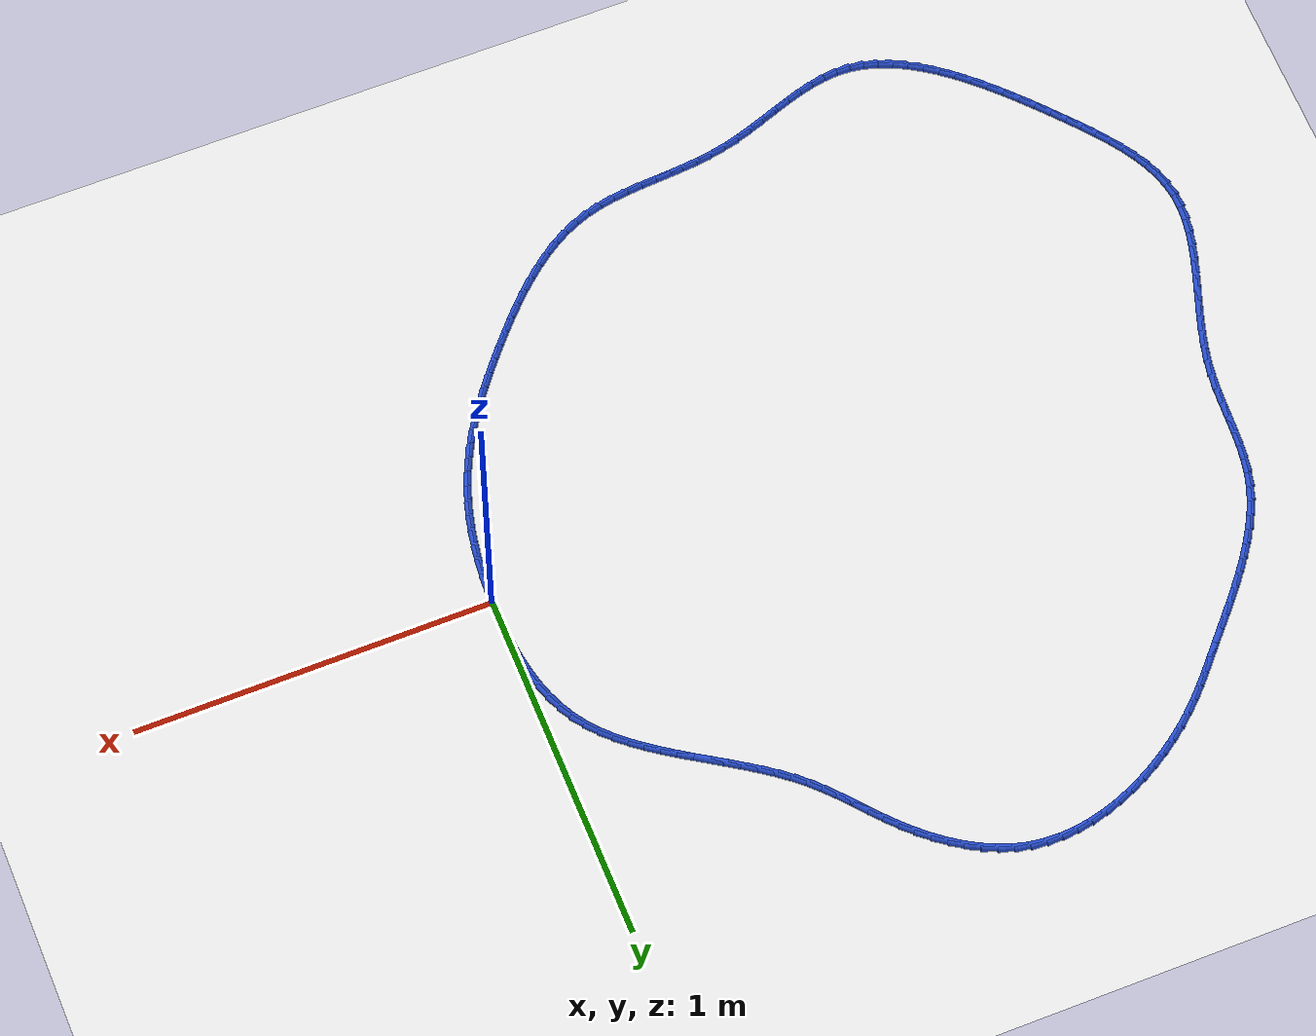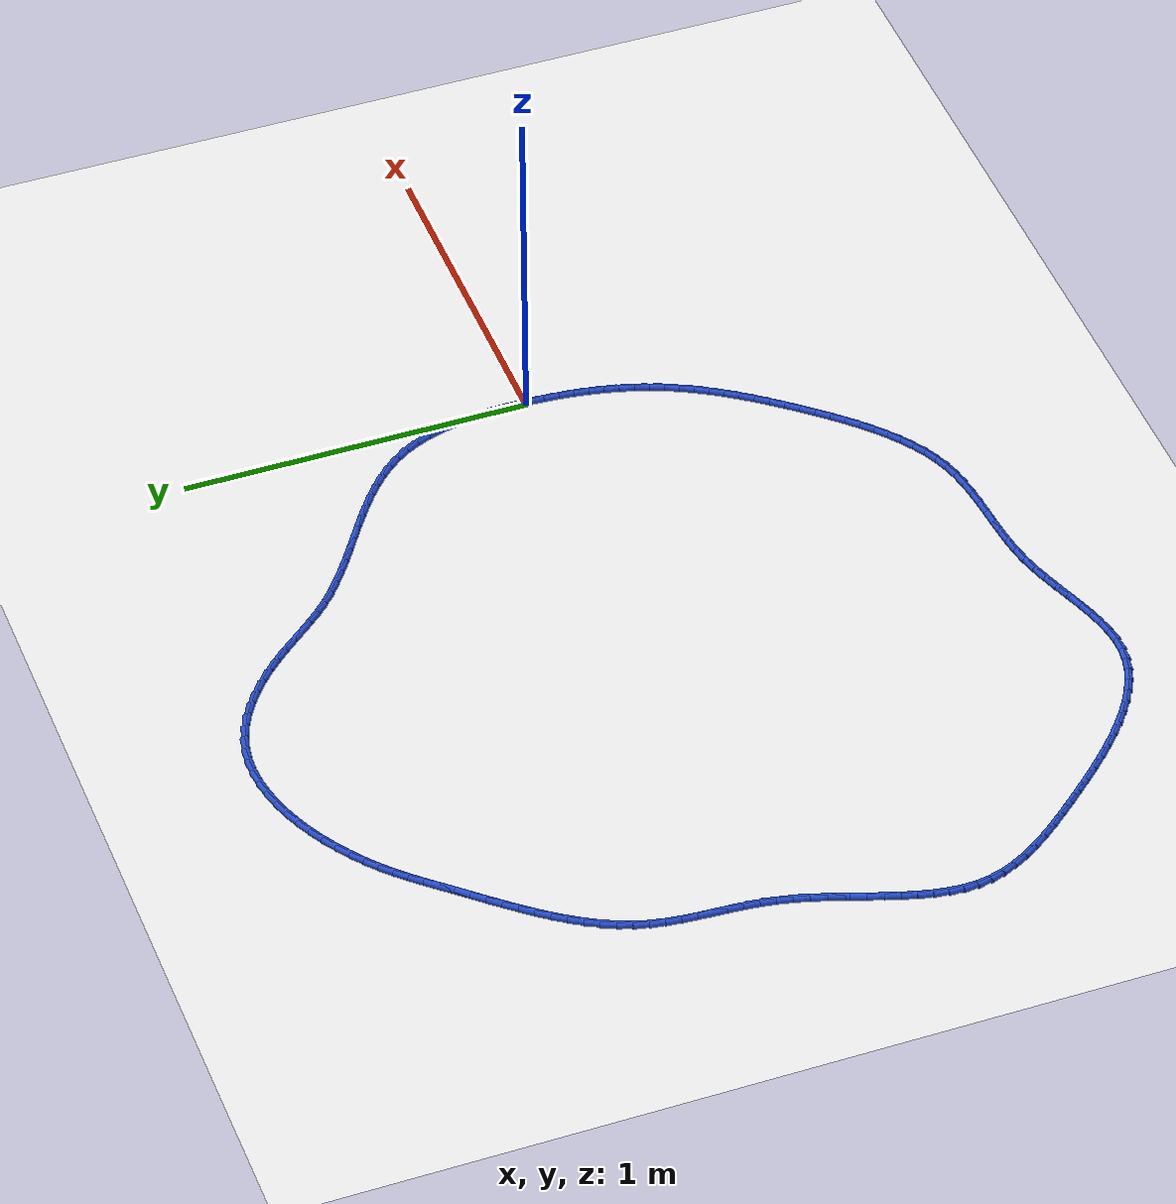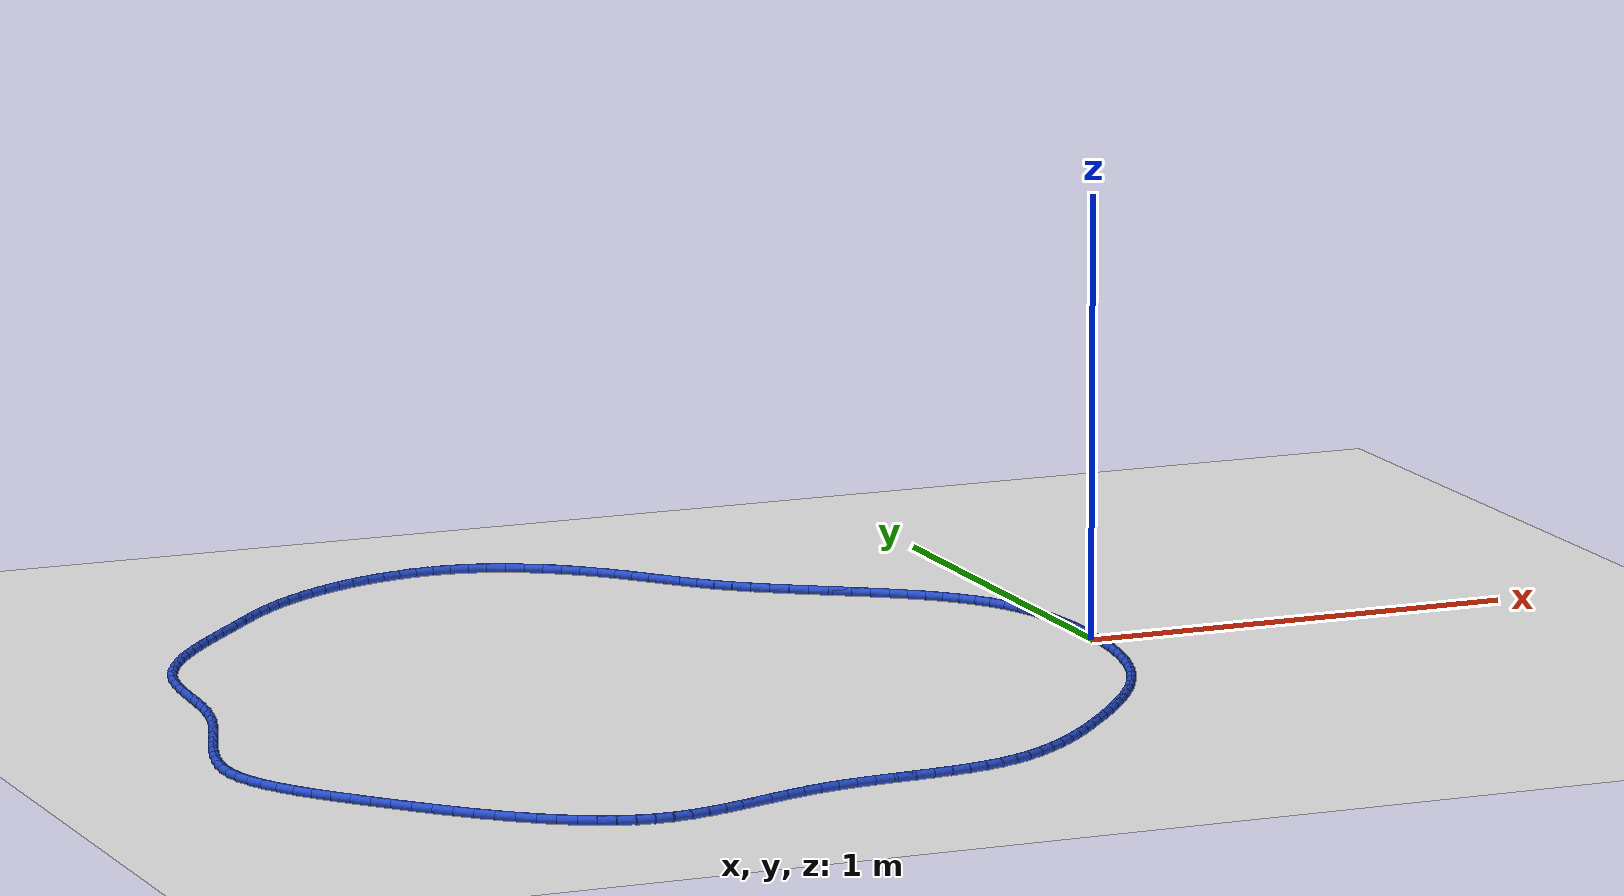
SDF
<sdf version="1.6">
 <world name="default">
  <light name="sun" type="directional">
   <pose>0 0 10 0 -0 0</pose>
   <diffuse>0.8 0.8 0.8 1</diffuse>
   <specular>0.2 0.2 0.2 1</specular>
   <attenuation>
    <range>1000</range>
    <constant>0.9</constant>
    <linear>0.01</linear>
    <quadratic>0.001</quadratic>
   </attenuation>
   <direction>-0.5 0.1 -0.9</direction>
  </light>
  <model name="ground_plane">
   <static>1</static>
   <link name="link">
    <collision name="collision">
     <geometry><plane><normal>0 0 1</normal><size>100 100</size></plane></geometry>
     <surface><friction><ode><mu>100</mu><mu2>50</mu2></ode></friction></surface>
    </collision>
    <visual name="visual">
     <cast_shadows>0</cast_shadows>
     <geometry><plane><normal>0 0 1</normal><size>100 100</size></plane></geometry>
     <material>
      <script><uri>file://media/materials/scripts/gazebo.material</uri><name>Gazebo/WhiteGlow</name></script>
     </material>
    </visual>
   </link>
  </model>
  <gravity>0 0 -9.8</gravity>
  <magnetic_field>6e-06 2.3e-05 -4.2e-05</magnetic_field>
  <atmosphere type="adiabatic"/>
  <physics name="default_physics" default="0" type="ode">
   <max_step_size>0.001</max_step_size>
   <real_time_factor>1</real_time_factor>
   <real_time_update_rate>1000</real_time_update_rate>
  </physics>
  <scene><ambient>0.4 0.4 0.4 1</ambient><background>0.7 0.7 0.7 1</background><shadows>1</shadows></scene>
  <spherical_coordinates>
   <surface_model>EARTH_WGS84</surface_model>
   <latitude_deg>0</latitude_deg>
   <longitude_deg>0</longitude_deg>
   <elevation>0</elevation>
   <heading_deg>0</heading_deg>
  </spherical_coordinates>
  <model name="line">
   <link name="link_0">
    <pose>5.898059818321144e-17 -1.1102230246251565e-16 0.01 0 1.57 1.56180621428713</pose>
    <collision name="collision">
     <geometry><cylinder><radius>0.01</radius><length>0.08</length></cylinder></geometry>
    </collision>
    <visual name="visual">
     <material>
      <script><name>Gazebo/Blue</name><uri>file://media/materials/scripts/gazebo.material</uri></script>
     </material>
     <geometry><cylinder><radius>0.01</radius><length>0.08</length></cylinder></geometry>
    </visual>
   </link>
   <link name="link_1">
    <pose>0.00040379242468226585 0.04491395917694073 0.01 0 1.57 -1.5439375213575095</pose>
    <collision name="collision">
     <geometry><cylinder><radius>0.01</radius><length>0.08</length></cylinder></geometry>
    </collision>
    <visual name="visual">
     <material>
      <script><name>Gazebo/Blue</name><uri>file://media/materials/scripts/gazebo.material</uri></script>
     </material>
     <geometry><cylinder><radius>0.01</radius><length>0.08</length></cylinder></geometry>
    </visual>
   </link>
   <link name="link_2">
    <pose>-0.0008047868837613741 0.08990064617186799 0.01 0 1.57 -1.5024942950736468</pose>
    <collision name="collision">
     <geometry><cylinder><radius>0.01</radius><length>0.08</length></cylinder></geometry>
    </collision>
    <visual name="visual">
     <material>
      <script><name>Gazebo/Blue</name><uri>file://media/materials/scripts/gazebo.material</uri></script>
     </material>
     <geometry><cylinder><radius>0.01</radius><length>0.08</length></cylinder></geometry>
    </visual>
   </link>
   <link name="link_3">
    <pose>-0.003865403800621507 0.13464098447116502 0.01 0 1.57 -1.4546864012592606</pose>
    <collision name="collision">
     <geometry><cylinder><radius>0.01</radius><length>0.08</length></cylinder></geometry>
    </collision>
    <visual name="visual">
     <material>
      <script><name>Gazebo/Blue</name><uri>file://media/materials/scripts/gazebo.material</uri></script>
     </material>
     <geometry><cylinder><radius>0.01</radius><length>0.08</length></cylinder></geometry>
    </visual>
   </link>
   <link name="link_4">
    <pose>-0.009017724201188775 0.17881589756121483 0.01 0 1.57 -1.3996163998209812</pose>
    <collision name="collision">
     <geometry><cylinder><radius>0.01</radius><length>0.08</length></cylinder></geometry>
    </collision>
    <visual name="visual">
     <material>
      <script><name>Gazebo/Blue</name><uri>file://media/materials/scripts/gazebo.material</uri></script>
     </material>
     <geometry><cylinder><radius>0.01</radius><length>0.08</length></cylinder></geometry>
    </visual>
   </link>
   <link name="link_5">
    <pose>-0.01650141396075381 0.22210630892840083 0.01 0 1.57 -1.336287637648683</pose>
    <collision name="collision">
     <geometry><cylinder><radius>0.01</radius><length>0.08</length></cylinder></geometry>
    </collision>
    <visual name="visual">
     <material>
      <script><name>Gazebo/Blue</name><uri>file://media/materials/scripts/gazebo.material</uri></script>
     </material>
     <geometry><cylinder><radius>0.01</radius><length>0.08</length></cylinder></geometry>
    </visual>
   </link>
   <link name="link_6">
    <pose>-0.02655613895460727 0.2641931420591062 0.01 0 1.57 -1.2636696546748554</pose>
    <collision name="collision">
     <geometry><cylinder><radius>0.01</radius><length>0.08</length></cylinder></geometry>
    </collision>
    <visual name="visual">
     <material>
      <script><name>Gazebo/Blue</name><uri>file://media/materials/scripts/gazebo.material</uri></script>
     </material>
     <geometry><cylinder><radius>0.01</radius><length>0.08</length></cylinder></geometry>
    </visual>
   </link>
   <link name="link_7">
    <pose>-0.03942156505803979 0.30475732043971426 0.01 0 1.57 -1.180824143735732</pose>
    <collision name="collision">
     <geometry><cylinder><radius>0.01</radius><length>0.08</length></cylinder></geometry>
    </collision>
    <visual name="visual">
     <material>
      <script><name>Gazebo/Blue</name><uri>file://media/materials/scripts/gazebo.material</uri></script>
     </material>
     <geometry><cylinder><radius>0.01</radius><length>0.08</length></cylinder></geometry>
    </visual>
   </link>
   <link name="link_8">
    <pose>-0.05533735814634197 0.34347976755660786 0.01 0 1.57 -1.0871142439543904</pose>
    <collision name="collision">
     <geometry><cylinder><radius>0.01</radius><length>0.08</length></cylinder></geometry>
    </collision>
    <visual name="visual">
     <material>
      <script><name>Gazebo/Blue</name><uri>file://media/materials/scripts/gazebo.material</uri></script>
     </material>
     <geometry><cylinder><radius>0.01</radius><length>0.08</length></cylinder></geometry>
    </visual>
   </link>
   <link name="link_9">
    <pose>-0.0745431840948045 0.38004140689617066 0.01 0 1.57 -0.9852484915830972</pose>
    <collision name="collision">
     <geometry><cylinder><radius>0.01</radius><length>0.08</length></cylinder></geometry>
    </collision>
    <visual name="visual">
     <material>
      <script><name>Gazebo/Blue</name><uri>file://media/materials/scripts/gazebo.material</uri></script>
     </material>
     <geometry><cylinder><radius>0.01</radius><length>0.08</length></cylinder></geometry>
    </visual>
   </link>
   <link name="link_10">
    <pose>-0.097196464191529 0.41420272313641987 0.01 0 1.57 -0.8901639784117636</pose>
    <collision name="collision">
     <geometry><cylinder><radius>0.01</radius><length>0.08</length></cylinder></geometry>
    </collision>
    <visual name="visual">
     <material>
      <script><name>Gazebo/Blue</name><uri>file://media/materials/scripts/gazebo.material</uri></script>
     </material>
     <geometry><cylinder><radius>0.01</radius><length>0.08</length></cylinder></geometry>
    </visual>
   </link>
   <link name="link_11">
    <pose>-0.12304247689613815 0.446122896792728 0.01 0 1.57 -0.8077023309881043</pose>
    <collision name="collision">
     <geometry><cylinder><radius>0.01</radius><length>0.08</length></cylinder></geometry>
    </collision>
    <visual name="visual">
     <material>
      <script><name>Gazebo/Blue</name><uri>file://media/materials/scripts/gazebo.material</uri></script>
     </material>
     <geometry><cylinder><radius>0.01</radius><length>0.08</length></cylinder></geometry>
    </visual>
   </link>
   <link name="link_12">
    <pose>-0.15169767128786021 0.476085734442461 0.01 0 1.57 -0.738415332042732</pose>
    <collision name="collision">
     <geometry><cylinder><radius>0.01</radius><length>0.08</length></cylinder></geometry>
    </collision>
    <visual name="visual">
     <material>
      <script><name>Gazebo/Blue</name><uri>file://media/materials/scripts/gazebo.material</uri></script>
     </material>
     <geometry><cylinder><radius>0.01</radius><length>0.08</length></cylinder></geometry>
    </visual>
   </link>
   <link name="link_13">
    <pose>-0.18277845282651323 0.5043750848592243 0.01 0 1.57 -0.6820884298924055</pose>
    <collision name="collision">
     <geometry><cylinder><radius>0.01</radius><length>0.08</length></cylinder></geometry>
    </collision>
    <visual name="visual">
     <material>
      <script><name>Gazebo/Blue</name><uri>file://media/materials/scripts/gazebo.material</uri></script>
     </material>
     <geometry><cylinder><radius>0.01</radius><length>0.08</length></cylinder></geometry>
    </visual>
   </link>
   <link name="link_14">
    <pose>-0.2159012269719153 0.5312747968166227 0.01 0 1.57 -0.6381071993134898</pose>
    <collision name="collision">
     <geometry><cylinder><radius>0.01</radius><length>0.08</length></cylinder></geometry>
    </collision>
    <visual name="visual">
     <material>
      <script><name>Gazebo/Blue</name><uri>file://media/materials/scripts/gazebo.material</uri></script>
     </material>
     <geometry><cylinder><radius>0.01</radius><length>0.08</length></cylinder></geometry>
    </visual>
   </link>
   <link name="link_15">
    <pose>-0.2506823991838844 0.5570687190882618 0.01 0 1.57 -0.6057349746156875</pose>
    <collision name="collision">
     <geometry><cylinder><radius>0.01</radius><length>0.08</length></cylinder></geometry>
    </collision>
    <visual name="visual">
     <material>
      <script><name>Gazebo/Blue</name><uri>file://media/materials/scripts/gazebo.material</uri></script>
     </material>
     <geometry><cylinder><radius>0.01</radius><length>0.08</length></cylinder></geometry>
    </visual>
   </link>
   <link name="link_16">
    <pose>-0.28673837492223875 0.5820407004477464 0.01 0 1.57 -0.5842914925208349</pose>
    <collision name="collision">
     <geometry><cylinder><radius>0.01</radius><length>0.08</length></cylinder></geometry>
    </collision>
    <visual name="visual">
     <material>
      <script><name>Gazebo/Blue</name><uri>file://media/materials/scripts/gazebo.material</uri></script>
     </material>
     <geometry><cylinder><radius>0.01</radius><length>0.08</length></cylinder></geometry>
    </visual>
   </link>
   <link name="link_17">
    <pose>-0.3236855596467963 0.6064745896686818 0.01 0 1.57 -0.5732537579557585</pose>
    <collision name="collision">
     <geometry><cylinder><radius>0.01</radius><length>0.08</length></cylinder></geometry>
    </collision>
    <visual name="visual">
     <material>
      <script><name>Gazebo/Blue</name><uri>file://media/materials/scripts/gazebo.material</uri></script>
     </material>
     <geometry><cylinder><radius>0.01</radius><length>0.08</length></cylinder></geometry>
    </visual>
   </link>
   <link name="link_18">
    <pose>-0.3611403588173749 0.6306542355246728 0.01 0 1.57 -0.5723054349931989</pose>
    <collision name="collision">
     <geometry><cylinder><radius>0.01</radius><length>0.08</length></cylinder></geometry>
    </collision>
    <visual name="visual">
     <material>
      <script><name>Gazebo/Blue</name><uri>file://media/materials/scripts/gazebo.material</uri></script>
     </material>
     <geometry><cylinder><radius>0.01</radius><length>0.08</length></cylinder></geometry>
    </visual>
   </link>
   <link name="link_19">
    <pose>-0.39871917789379296 0.654863486789325 0.01 0 1.57 -0.5813545546562985</pose>
    <collision name="collision">
     <geometry><cylinder><radius>0.01</radius><length>0.08</length></cylinder></geometry>
    </collision>
    <visual name="visual">
     <material>
      <script><name>Gazebo/Blue</name><uri>file://media/materials/scripts/gazebo.material</uri></script>
     </material>
     <geometry><cylinder><radius>0.01</radius><length>0.08</length></cylinder></geometry>
    </visual>
   </link>
   <link name="link_20">
    <pose>-0.4360384223358684 0.6793861922362435 0.01 0 1.57 -0.6005301611040683</pose>
    <collision name="collision">
     <geometry><cylinder><radius>0.01</radius><length>0.08</length></cylinder></geometry>
    </collision>
    <visual name="visual">
     <material>
      <script><name>Gazebo/Blue</name><uri>file://media/materials/scripts/gazebo.material</uri></script>
     </material>
     <geometry><cylinder><radius>0.01</radius><length>0.08</length></cylinder></geometry>
    </visual>
   </link>
   <link name="link_21">
    <pose>-0.4727144976034193 0.7045062006390335 0.01 0 1.57 -0.630159722550051</pose>
    <collision name="collision">
     <geometry><cylinder><radius>0.01</radius><length>0.08</length></cylinder></geometry>
    </collision>
    <visual name="visual">
     <material>
      <script><name>Gazebo/Blue</name><uri>file://media/materials/scripts/gazebo.material</uri></script>
     </material>
     <geometry><cylinder><radius>0.01</radius><length>0.08</length></cylinder></geometry>
    </visual>
   </link>
   <link name="link_22">
    <pose>-0.5083638091562636 0.7305073607712995 0.01 0 1.57 -0.6707210525257213</pose>
    <collision name="collision">
     <geometry><cylinder><radius>0.01</radius><length>0.08</length></cylinder></geometry>
    </collision>
    <visual name="visual">
     <material>
      <script><name>Gazebo/Blue</name><uri>file://media/materials/scripts/gazebo.material</uri></script>
     </material>
     <geometry><cylinder><radius>0.01</radius><length>0.08</length></cylinder></geometry>
    </visual>
   </link>
   <link name="link_23">
    <pose>-0.5426027624542193 0.7576735214066475 0.01 0 1.57 -0.722755208579692</pose>
    <collision name="collision">
     <geometry><cylinder><radius>0.01</radius><length>0.08</length></cylinder></geometry>
    </collision>
    <visual name="visual">
     <material>
      <script><name>Gazebo/Blue</name><uri>file://media/materials/scripts/gazebo.material</uri></script>
     </material>
     <geometry><cylinder><radius>0.01</radius><length>0.08</length></cylinder></geometry>
    </visual>
   </link>
   <link name="link_24">
    <pose>-0.5750477629571047 0.7862885313186818 0.01 0 1.57 -0.783985759773363</pose>
    <collision name="collision">
     <geometry><cylinder><radius>0.01</radius><length>0.08</length></cylinder></geometry>
    </collision>
    <visual name="visual">
     <material>
      <script><name>Gazebo/Blue</name><uri>file://media/materials/scripts/gazebo.material</uri></script>
     </material>
     <geometry><cylinder><radius>0.01</radius><length>0.08</length></cylinder></geometry>
    </visual>
   </link>
   <link name="link_25">
    <pose>-0.6054123855893518 0.8165675006648849 0.01 0 1.57 -0.834698354072756</pose>
    <collision name="collision">
     <geometry><cylinder><radius>0.01</radius><length>0.08</length></cylinder></geometry>
    </collision>
    <visual name="visual">
     <material>
      <script><name>Gazebo/Blue</name><uri>file://media/materials/scripts/gazebo.material</uri></script>
     </material>
     <geometry><cylinder><radius>0.01</radius><length>0.08</length></cylinder></geometry>
    </visual>
   </link>
   <link name="link_26">
    <pose>-0.6341025545493222 0.8482357650511061 0.01 0 1.57 -0.8656365697440467</pose>
    <collision name="collision">
     <geometry><cylinder><radius>0.01</radius><length>0.08</length></cylinder></geometry>
    </collision>
    <visual name="visual">
     <material>
      <script><name>Gazebo/Blue</name><uri>file://media/materials/scripts/gazebo.material</uri></script>
     </material>
     <geometry><cylinder><radius>0.01</radius><length>0.08</length></cylinder></geometry>
    </visual>
   </link>
   <link name="link_27">
    <pose>-0.6618246935859582 0.8808060838038596 0.01 0 1.57 -0.8765080178297449</pose>
    <collision name="collision">
     <geometry><cylinder><radius>0.01</radius><length>0.08</length></cylinder></geometry>
    </collision>
    <visual name="visual">
     <material>
      <script><name>Gazebo/Blue</name><uri>file://media/materials/scripts/gazebo.material</uri></script>
     </material>
     <geometry><cylinder><radius>0.01</radius><length>0.08</length></cylinder></geometry>
    </visual>
   </link>
   <link name="link_28">
    <pose>-0.6892864458568106 0.9137903536282546 0.01 0 1.57 -0.8674427906371375</pose>
    <collision name="collision">
     <geometry><cylinder><radius>0.01</radius><length>0.08</length></cylinder></geometry>
    </collision>
    <visual name="visual">
     <material>
      <script><name>Gazebo/Blue</name><uri>file://media/materials/scripts/gazebo.material</uri></script>
     </material>
     <geometry><cylinder><radius>0.01</radius><length>0.08</length></cylinder></geometry>
    </visual>
   </link>
   <link name="link_29">
    <pose>-0.7171954545194295 0.9467004712293997 0.01 0 1.57 -0.8388216203982715</pose>
    <collision name="collision">
     <geometry><cylinder><radius>0.01</radius><length>0.08</length></cylinder></geometry>
    </collision>
    <visual name="visual">
     <material>
      <script><name>Gazebo/Blue</name><uri>file://media/materials/scripts/gazebo.material</uri></script>
     </material>
     <geometry><cylinder><radius>0.01</radius><length>0.08</length></cylinder></geometry>
    </visual>
   </link>
   <link name="link_30">
    <pose>-0.7462593627313647 0.9790483333124035 0.01 0 1.57 -0.7926557752086739</pose>
    <collision name="collision">
     <geometry><cylinder><radius>0.01</radius><length>0.08</length></cylinder></geometry>
    </collision>
    <visual name="visual">
     <material>
      <script><name>Gazebo/Blue</name><uri>file://media/materials/scripts/gazebo.material</uri></script>
     </material>
     <geometry><cylinder><radius>0.01</radius><length>0.08</length></cylinder></geometry>
    </visual>
   </link>
   <link name="link_31">
    <pose>-0.7771070527146782 1.0103470658249196 0.01 0 1.57 -0.7382358331725314</pose>
    <collision name="collision">
     <geometry><cylinder><radius>0.01</radius><length>0.08</length></cylinder></geometry>
    </collision>
    <visual name="visual">
     <material>
      <script><name>Gazebo/Blue</name><uri>file://media/materials/scripts/gazebo.material</uri></script>
     </material>
     <geometry><cylinder><radius>0.01</radius><length>0.08</length></cylinder></geometry>
    </visual>
   </link>
   <link name="link_32">
    <pose>-0.8098276493996408 1.0401182188479947 0.01 0 1.57 -0.6783333662681563</pose>
    <collision name="collision">
     <geometry><cylinder><radius>0.01</radius><length>0.08</length></cylinder></geometry>
    </collision>
    <visual name="visual">
     <material>
      <script><name>Gazebo/Blue</name><uri>file://media/materials/scripts/gazebo.material</uri></script>
     </material>
     <geometry><cylinder><radius>0.01</radius><length>0.08</length></cylinder></geometry>
    </visual>
   </link>
   <link name="link_33">
    <pose>-0.8442839836222729 1.067886874293862 0.01 0 1.57 -0.6117185717407283</pose>
    <collision name="collision">
     <geometry><cylinder><radius>0.01</radius><length>0.08</length></cylinder></geometry>
    </collision>
    <visual name="visual">
     <material>
      <script><name>Gazebo/Blue</name><uri>file://media/materials/scripts/gazebo.material</uri></script>
     </material>
     <geometry><cylinder><radius>0.01</radius><length>0.08</length></cylinder></geometry>
    </visual>
   </link>
   <link name="link_34">
    <pose>-0.8803381139421738 1.0931781261278755 0.01 0 1.57 -0.537091593927464</pose>
    <collision name="collision">
     <geometry><cylinder><radius>0.01</radius><length>0.08</length></cylinder></geometry>
    </collision>
    <visual name="visual">
     <material>
      <script><name>Gazebo/Blue</name><uri>file://media/materials/scripts/gazebo.material</uri></script>
     </material>
     <geometry><cylinder><radius>0.01</radius><length>0.08</length></cylinder></geometry>
    </visual>
   </link>
   <link name="link_35">
    <pose>-0.9178520989189433 1.1155170683153879 0.01 0 1.57 -0.4531654059440723</pose>
    <collision name="collision">
     <geometry><cylinder><radius>0.01</radius><length>0.08</length></cylinder></geometry>
    </collision>
    <visual name="visual">
     <material>
      <script><name>Gazebo/Blue</name><uri>file://media/materials/scripts/gazebo.material</uri></script>
     </material>
     <geometry><cylinder><radius>0.01</radius><length>0.08</length></cylinder></geometry>
    </visual>
   </link>
   <link name="link_36">
    <pose>-0.9566879971121814 1.1344287948217533 0.01 0 1.57 -0.35881784714192916</pose>
    <collision name="collision">
     <geometry><cylinder><radius>0.01</radius><length>0.08</length></cylinder></geometry>
    </collision>
    <visual name="visual">
     <material>
      <script><name>Gazebo/Blue</name><uri>file://media/materials/scripts/gazebo.material</uri></script>
     </material>
     <geometry><cylinder><radius>0.01</radius><length>0.08</length></cylinder></geometry>
    </visual>
   </link>
   <link name="link_37">
    <pose>-0.996707867081488 1.149438399612325 0.01 0 1.57 -0.2533835315275436</pose>
    <collision name="collision">
     <geometry><cylinder><radius>0.01</radius><length>0.08</length></cylinder></geometry>
    </collision>
    <visual name="visual">
     <material>
      <script><name>Gazebo/Blue</name><uri>file://media/materials/scripts/gazebo.material</uri></script>
     </material>
     <geometry><cylinder><radius>0.01</radius><length>0.08</length></cylinder></geometry>
    </visual>
   </link>
   <link name="link_38">
    <pose>-1.0377735951084934 1.160072336522778 0.01 0 1.57 -0.1422656179847581</pose>
    <collision name="collision">
     <geometry><cylinder><radius>0.01</radius><length>0.08</length></cylinder></geometry>
    </collision>
    <visual name="visual">
     <material>
      <script><name>Gazebo/Blue</name><uri>file://media/materials/scripts/gazebo.material</uri></script>
     </material>
     <geometry><cylinder><radius>0.01</radius><length>0.08</length></cylinder></geometry>
    </visual>
   </link>
   <link name="link_39">
    <pose>-1.0797187879673418 1.1660802827238308 0.01 0 1.57 -0.037565053827910075</pose>
    <collision name="collision">
     <geometry><cylinder><radius>0.01</radius><length>0.08</length></cylinder></geometry>
    </collision>
    <visual name="visual">
     <material>
      <script><name>Gazebo/Blue</name><uri>file://media/materials/scripts/gazebo.material</uri></script>
     </material>
     <geometry><cylinder><radius>0.01</radius><length>0.08</length></cylinder></geometry>
    </visual>
   </link>
   <link name="link_40">
    <pose>-1.1223175922608086 1.167681262236125 0.01 0 1.57 0.05868972124511242</pose>
    <collision name="collision">
     <geometry><cylinder><radius>0.01</radius><length>0.08</length></cylinder></geometry>
    </collision>
    <visual name="visual">
     <material>
      <script><name>Gazebo/Blue</name><uri>file://media/materials/scripts/gazebo.material</uri></script>
     </material>
     <geometry><cylinder><radius>0.01</radius><length>0.08</length></cylinder></geometry>
    </visual>
   </link>
   <link name="link_41">
    <pose>-1.165336644057373 1.1651535832285251 0.01 0 1.57 0.146560812369361</pose>
    <collision name="collision">
     <geometry><cylinder><radius>0.01</radius><length>0.08</length></cylinder></geometry>
    </collision>
    <visual name="visual">
     <material>
      <script><name>Gazebo/Blue</name><uri>file://media/materials/scripts/gazebo.material</uri></script>
     </material>
     <geometry><cylinder><radius>0.01</radius><length>0.08</length></cylinder></geometry>
    </visual>
   </link>
   <link name="link_42">
    <pose>-1.2085425794255127 1.158775553869897 0.01 0 1.57 0.2265831939596096</pose>
    <collision name="collision">
     <geometry><cylinder><radius>0.01</radius><length>0.08</length></cylinder></geometry>
    </collision>
    <visual name="visual">
     <material>
      <script><name>Gazebo/Blue</name><uri>file://media/materials/scripts/gazebo.material</uri></script>
     </material>
     <geometry><cylinder><radius>0.01</radius><length>0.08</length></cylinder></geometry>
    </visual>
   </link>
   <link name="link_43">
    <pose>-1.2517020344337073 1.1488254823291062 0.01 0 1.57 0.29956547524877053</pose>
    <collision name="collision">
     <geometry><cylinder><radius>0.01</radius><length>0.08</length></cylinder></geometry>
    </collision>
    <visual name="visual">
     <material>
      <script><name>Gazebo/Blue</name><uri>file://media/materials/scripts/gazebo.material</uri></script>
     </material>
     <geometry><cylinder><radius>0.01</radius><length>0.08</length></cylinder></geometry>
    </visual>
   </link>
   <link name="link_44">
    <pose>-1.2945816451504368 1.1355816767750189 0.01 0 1.57 0.36644288319329077</pose>
    <collision name="collision">
     <geometry><cylinder><radius>0.01</radius><length>0.08</length></cylinder></geometry>
    </collision>
    <visual name="visual">
     <material>
      <script><name>Gazebo/Blue</name><uri>file://media/materials/scripts/gazebo.material</uri></script>
     </material>
     <geometry><cylinder><radius>0.01</radius><length>0.08</length></cylinder></geometry>
    </visual>
   </link>
   <link name="link_45">
    <pose>-1.3369480476441784 1.1193224453765 0.01 0 1.57 0.42818445335033456</pose>
    <collision name="collision">
     <geometry><cylinder><radius>0.01</radius><length>0.08</length></cylinder></geometry>
    </collision>
    <visual name="visual">
     <material>
      <script><name>Gazebo/Blue</name><uri>file://media/materials/scripts/gazebo.material</uri></script>
     </material>
     <geometry><cylinder><radius>0.01</radius><length>0.08</length></cylinder></geometry>
    </visual>
   </link>
   <link name="link_46">
    <pose>-1.378567877983412 1.100326096302415 0.01 0 1.57 0.48574382314129827</pose>
    <collision name="collision">
     <geometry><cylinder><radius>0.01</radius><length>0.08</length></cylinder></geometry>
    </collision>
    <visual name="visual">
     <material>
      <script><name>Gazebo/Blue</name><uri>file://media/materials/scripts/gazebo.material</uri></script>
     </material>
     <geometry><cylinder><radius>0.01</radius><length>0.08</length></cylinder></geometry>
    </visual>
   </link>
   <link name="link_47">
    <pose>-1.4192077722366159 1.07887093772163 0.01 0 1.57 0.5400408883932873</pose>
    <collision name="collision">
     <geometry><cylinder><radius>0.01</radius><length>0.08</length></cylinder></geometry>
    </collision>
    <visual name="visual">
     <material>
      <script><name>Gazebo/Blue</name><uri>file://media/materials/scripts/gazebo.material</uri></script>
     </material>
     <geometry><cylinder><radius>0.01</radius><length>0.08</length></cylinder></geometry>
    </visual>
   </link>
   <link name="link_48">
    <pose>-1.4586343664722698 1.05523527780301 0.01 0 1.57 0.5919640210015958</pose>
    <collision name="collision">
     <geometry><cylinder><radius>0.01</radius><length>0.08</length></cylinder></geometry>
    </collision>
    <visual name="visual">
     <material>
      <script><name>Gazebo/Blue</name><uri>file://media/materials/scripts/gazebo.material</uri></script>
     </material>
     <geometry><cylinder><radius>0.01</radius><length>0.08</length></cylinder></geometry>
    </visual>
   </link>
   <link name="link_49">
    <pose>-1.4966142967588516 1.0296974247154211 0.01 0 1.57 0.6423861035709708</pose>
    <collision name="collision">
     <geometry><cylinder><radius>0.01</radius><length>0.08</length></cylinder></geometry>
    </collision>
    <visual name="visual">
     <material>
      <script><name>Gazebo/Blue</name><uri>file://media/materials/scripts/gazebo.material</uri></script>
     </material>
     <geometry><cylinder><radius>0.01</radius><length>0.08</length></cylinder></geometry>
    </visual>
   </link>
   <link name="link_50">
    <pose>-1.532914199164841 1.0025356866277286 0.01 0 1.57 0.6921909143759554</pose>
    <collision name="collision">
     <geometry><cylinder><radius>0.01</radius><length>0.08</length></cylinder></geometry>
    </collision>
    <visual name="visual">
     <material>
      <script><name>Gazebo/Blue</name><uri>file://media/materials/scripts/gazebo.material</uri></script>
     </material>
     <geometry><cylinder><radius>0.01</radius><length>0.08</length></cylinder></geometry>
    </visual>
   </link>
   <link name="link_51">
    <pose>-1.5673007097587162 0.9740283717087979 0.01 0 1.57 0.7418429253149657</pose>
    <collision name="collision">
     <geometry><cylinder><radius>0.01</radius><length>0.08</length></cylinder></geometry>
    </collision>
    <visual name="visual">
     <material>
      <script><name>Gazebo/Blue</name><uri>file://media/materials/scripts/gazebo.material</uri></script>
     </material>
     <geometry><cylinder><radius>0.01</radius><length>0.08</length></cylinder></geometry>
    </visual>
   </link>
   <link name="link_52">
    <pose>-1.5995767513322727 0.9444481973041711 0.01 0 1.57 0.785534623938228</pose>
    <collision name="collision">
     <geometry><cylinder><radius>0.01</radius><length>0.08</length></cylinder></geometry>
    </collision>
    <visual name="visual">
     <material>
      <script><name>Gazebo/Blue</name><uri>file://media/materials/scripts/gazebo.material</uri></script>
     </material>
     <geometry><cylinder><radius>0.01</radius><length>0.08</length></cylinder></geometry>
    </visual>
   </link>
   <link name="link_53">
    <pose>-1.6300222513085243 0.9139943869750505 0.01 0 1.57 0.8176490082176219</pose>
    <collision name="collision">
     <geometry><cylinder><radius>0.01</radius><length>0.08</length></cylinder></geometry>
    </collision>
    <visual name="visual">
     <material>
      <script><name>Gazebo/Blue</name><uri>file://media/materials/scripts/gazebo.material</uri></script>
     </material>
     <geometry><cylinder><radius>0.01</radius><length>0.08</length></cylinder></geometry>
    </visual>
   </link>
   <link name="link_54">
    <pose>-1.6592532820447115 0.8828143732481583 0.01 0 1.57 0.837011709031941</pose>
    <collision name="collision">
     <geometry><cylinder><radius>0.01</radius><length>0.08</length></cylinder></geometry>
    </collision>
    <visual name="visual">
     <material>
      <script><name>Gazebo/Blue</name><uri>file://media/materials/scripts/gazebo.material</uri></script>
     </material>
     <geometry><cylinder><radius>0.01</radius><length>0.08</length></cylinder></geometry>
    </visual>
   </link>
   <link name="link_55">
    <pose>-1.6878929444743165 0.851054505732709 0.01 0 1.57 0.8431993129954104</pose>
    <collision name="collision">
     <geometry><cylinder><radius>0.01</radius><length>0.08</length></cylinder></geometry>
    </collision>
    <visual name="visual">
     <material>
      <script><name>Gazebo/Blue</name><uri>file://media/materials/scripts/gazebo.material</uri></script>
     </material>
     <geometry><cylinder><radius>0.01</radius><length>0.08</length></cylinder></geometry>
    </visual>
   </link>
   <link name="link_56">
    <pose>-1.7165643395308186 0.818861134037916 0.01 0 1.57 0.839341410173947</pose>
    <collision name="collision">
     <geometry><cylinder><radius>0.01</radius><length>0.08</length></cylinder></geometry>
    </collision>
    <visual name="visual">
     <material>
      <script><name>Gazebo/Blue</name><uri>file://media/materials/scripts/gazebo.material</uri></script>
     </material>
     <geometry><cylinder><radius>0.01</radius><length>0.08</length></cylinder></geometry>
    </visual>
   </link>
   <link name="link_57">
    <pose>-1.745744537843145 0.7863498661139647 0.01 0 1.57 0.8391115784242851</pose>
    <collision name="collision">
     <geometry><cylinder><radius>0.01</radius><length>0.08</length></cylinder></geometry>
    </collision>
    <visual name="visual">
     <material>
      <script><name>Gazebo/Blue</name><uri>file://media/materials/scripts/gazebo.material</uri></script>
     </material>
     <geometry><cylinder><radius>0.01</radius><length>0.08</length></cylinder></geometry>
    </visual>
   </link>
   <link name="link_58">
    <pose>-1.7752455880747513 0.7534963124045471 0.01 0 1.57 0.8461688934546002</pose>
    <collision name="collision">
     <geometry><cylinder><radius>0.01</radius><length>0.08</length></cylinder></geometry>
    </collision>
    <visual name="visual">
     <material>
      <script><name>Gazebo/Blue</name><uri>file://media/materials/scripts/gazebo.material</uri></script>
     </material>
     <geometry><cylinder><radius>0.01</radius><length>0.08</length></cylinder></geometry>
    </visual>
   </link>
   <link name="link_59">
    <pose>-1.8046903331928204 0.7202362526002875 0.01 0 1.57 0.8604777571731997</pose>
    <collision name="collision">
     <geometry><cylinder><radius>0.01</radius><length>0.08</length></cylinder></geometry>
    </collision>
    <visual name="visual">
     <material>
      <script><name>Gazebo/Blue</name><uri>file://media/materials/scripts/gazebo.material</uri></script>
     </material>
     <geometry><cylinder><radius>0.01</radius><length>0.08</length></cylinder></geometry>
    </visual>
   </link>
   <link name="link_60">
    <pose>-1.8337016027327944 0.686505463564218 0.01 0 1.57 0.8821889055874872</pose>
    <collision name="collision">
     <geometry><cylinder><radius>0.01</radius><length>0.08</length></cylinder></geometry>
    </collision>
    <visual name="visual">
     <material>
      <script><name>Gazebo/Blue</name><uri>file://media/materials/scripts/gazebo.material</uri></script>
     </material>
     <geometry><cylinder><radius>0.01</radius><length>0.08</length></cylinder></geometry>
    </visual>
   </link>
   <link name="link_61">
    <pose>-1.861902226230116 0.6522397221593704 0.01 0 1.57 0.9116207322390194</pose>
    <collision name="collision">
     <geometry><cylinder><radius>0.01</radius><length>0.08</length></cylinder></geometry>
    </collision>
    <visual name="visual">
     <material>
      <script><name>Gazebo/Blue</name><uri>file://media/materials/scripts/gazebo.material</uri></script>
     </material>
     <geometry><cylinder><radius>0.01</radius><length>0.08</length></cylinder></geometry>
    </visual>
   </link>
   <link name="link_62">
    <pose>-1.888915033220227 0.6173748052487782 0.01 0 1.57 0.9492350208165029</pose>
    <collision name="collision">
     <geometry><cylinder><radius>0.01</radius><length>0.08</length></cylinder></geometry>
    </collision>
    <visual name="visual">
     <material>
      <script><name>Gazebo/Blue</name><uri>file://media/materials/scripts/gazebo.material</uri></script>
     </material>
     <geometry><cylinder><radius>0.01</radius><length>0.08</length></cylinder></geometry>
    </visual>
   </link>
   <link name="link_63">
    <pose>-1.9143628532385697 0.5818464896954726 0.01 0 1.57 0.9955988903554217</pose>
    <collision name="collision">
     <geometry><cylinder><radius>0.01</radius><length>0.08</length></cylinder></geometry>
    </collision>
    <visual name="visual">
     <material>
      <script><name>Gazebo/Blue</name><uri>file://media/materials/scripts/gazebo.material</uri></script>
     </material>
     <geometry><cylinder><radius>0.01</radius><length>0.08</length></cylinder></geometry>
    </visual>
   </link>
   <link name="link_64">
    <pose>-1.9378685158205866 0.545590552362487 0.01 0 1.57 1.0513211791074422</pose>
    <collision name="collision">
     <geometry><cylinder><radius>0.01</radius><length>0.08</length></cylinder></geometry>
    </collision>
    <visual name="visual">
     <material>
      <script><name>Gazebo/Blue</name><uri>file://media/materials/scripts/gazebo.material</uri></script>
     </material>
     <geometry><cylinder><radius>0.01</radius><length>0.08</length></cylinder></geometry>
    </visual>
   </link>
   <link name="link_65">
    <pose>-1.9590548505017196 0.5085427701128534 0.01 0 1.57 1.1169490594972817</pose>
    <collision name="collision">
     <geometry><cylinder><radius>0.01</radius><length>0.08</length></cylinder></geometry>
    </collision>
    <visual name="visual">
     <material>
      <script><name>Gazebo/Blue</name><uri>file://media/materials/scripts/gazebo.material</uri></script>
     </material>
     <geometry><cylinder><radius>0.01</radius><length>0.08</length></cylinder></geometry>
    </visual>
   </link>
   <link name="link_66">
    <pose>-1.9775446868174107 0.4706389198096039 0.01 0 1.57 1.1928124510432399</pose>
    <collision name="collision">
     <geometry><cylinder><radius>0.01</radius><length>0.08</length></cylinder></geometry>
    </collision>
    <visual name="visual">
     <material>
      <script><name>Gazebo/Blue</name><uri>file://media/materials/scripts/gazebo.material</uri></script>
     </material>
     <geometry><cylinder><radius>0.01</radius><length>0.08</length></cylinder></geometry>
    </visual>
   </link>
   <link name="link_67">
    <pose>-1.9929608543031023 0.4318147783157714 0.01 0 1.57 1.2787673944534794</pose>
    <collision name="collision">
     <geometry><cylinder><radius>0.01</radius><length>0.08</length></cylinder></geometry>
    </collision>
    <visual name="visual">
     <material>
      <script><name>Gazebo/Blue</name><uri>file://media/materials/scripts/gazebo.material</uri></script>
     </material>
     <geometry><cylinder><radius>0.01</radius><length>0.08</length></cylinder></geometry>
    </visual>
   </link>
   <link name="link_68">
    <pose>-2.0049281782285004 0.392006465010372 0.01 0 1.57 1.365439443051852</pose>
    <collision name="collision">
     <geometry><cylinder><radius>0.01</radius><length>0.08</length></cylinder></geometry>
    </collision>
    <visual name="visual">
     <material>
      <script><name>Gazebo/Blue</name><uri>file://media/materials/scripts/gazebo.material</uri></script>
     </material>
     <geometry><cylinder><radius>0.01</radius><length>0.08</length></cylinder></geometry>
    </visual>
   </link>
   <link name="link_69">
    <pose>-2.013425619933637 0.3512108775367873 0.01 0 1.57 1.4332689729244938</pose>
    <collision name="collision">
     <geometry><cylinder><radius>0.01</radius><length>0.08</length></cylinder></geometry>
    </collision>
    <visual name="visual">
     <material>
      <script><name>Gazebo/Blue</name><uri>file://media/materials/scripts/gazebo.material</uri></script>
     </material>
     <geometry><cylinder><radius>0.01</radius><length>0.08</length></cylinder></geometry>
    </visual>
   </link>
   <link name="link_70">
    <pose>-2.019190819043395 0.3095551209734152 0.01 0 1.57 1.4797491549518453</pose>
    <collision name="collision">
     <geometry><cylinder><radius>0.01</radius><length>0.08</length></cylinder></geometry>
    </collision>
    <visual name="visual">
     <material>
      <script><name>Gazebo/Blue</name><uri>file://media/materials/scripts/gazebo.material</uri></script>
     </material>
     <geometry><cylinder><radius>0.01</radius><length>0.08</length></cylinder></geometry>
    </visual>
   </link>
   <link name="link_71">
    <pose>-2.0230593661691905 0.2671831111430344 0.01 0 1.57 1.5055142459151896</pose>
    <collision name="collision">
     <geometry><cylinder><radius>0.01</radius><length>0.08</length></cylinder></geometry>
    </collision>
    <visual name="visual">
     <material>
      <script><name>Gazebo/Blue</name><uri>file://media/materials/scripts/gazebo.material</uri></script>
     </material>
     <geometry><cylinder><radius>0.01</radius><length>0.08</length></cylinder></geometry>
    </visual>
   </link>
   <link name="link_72">
    <pose>-2.0258668519224394 0.22423876386842448 0.01 0 1.57 1.511335716362047</pose>
    <collision name="collision">
     <geometry><cylinder><radius>0.01</radius><length>0.08</length></cylinder></geometry>
    </collision>
    <visual name="visual">
     <material>
      <script><name>Gazebo/Blue</name><uri>file://media/materials/scripts/gazebo.material</uri></script>
     </material>
     <geometry><cylinder><radius>0.01</radius><length>0.08</length></cylinder></geometry>
    </visual>
   </link>
   <link name="link_73">
    <pose>-2.0284488669145597 0.18086599497236386 0.01 0 1.57 1.497808161743431</pose>
    <collision name="collision">
     <geometry><cylinder><radius>0.01</radius><length>0.08</length></cylinder></geometry>
    </collision>
    <visual name="visual">
     <material>
      <script><name>Gazebo/Blue</name><uri>file://media/materials/scripts/gazebo.material</uri></script>
     </material>
     <geometry><cylinder><radius>0.01</radius><length>0.08</length></cylinder></geometry>
    </visual>
   </link>
   <link name="link_74">
    <pose>-2.031641001756967 0.13720872027763226 0.01 0 1.57 1.465297437117599</pose>
    <collision name="collision">
     <geometry><cylinder><radius>0.01</radius><length>0.08</length></cylinder></geometry>
    </collision>
    <visual name="visual">
     <material>
      <script><name>Gazebo/Blue</name><uri>file://media/materials/scripts/gazebo.material</uri></script>
     </material>
     <geometry><cylinder><radius>0.01</radius><length>0.08</length></cylinder></geometry>
    </visual>
   </link>
   <link name="link_75">
    <pose>-2.0362788470610775 0.09341085560700829 0.01 0 1.57 1.414108558348199</pose>
    <collision name="collision">
     <geometry><cylinder><radius>0.01</radius><length>0.08</length></cylinder></geometry>
    </collision>
    <visual name="visual">
     <material>
      <script><name>Gazebo/Blue</name><uri>file://media/materials/scripts/gazebo.material</uri></script>
     </material>
     <geometry><cylinder><radius>0.01</radius><length>0.08</length></cylinder></geometry>
    </visual>
   </link>
   <link name="link_76">
    <pose>-2.043197633596397 0.04961629181653965 0.01 0 1.57 1.3523382513944198</pose>
    <collision name="collision">
     <geometry><cylinder><radius>0.01</radius><length>0.08</length></cylinder></geometry>
    </collision>
    <visual name="visual">
     <material>
      <script><name>Gazebo/Blue</name><uri>file://media/materials/scripts/gazebo.material</uri></script>
     </material>
     <geometry><cylinder><radius>0.01</radius><length>0.08</length></cylinder></geometry>
    </visual>
   </link>
   <link name="link_77">
    <pose>-2.0528926280631867 0.0059453322055828695 0.01 0 1.57 1.3017079581913449</pose>
    <collision name="collision">
     <geometry><cylinder><radius>0.01</radius><length>0.08</length></cylinder></geometry>
    </collision>
    <visual name="visual">
     <material>
      <script><name>Gazebo/Blue</name><uri>file://media/materials/scripts/gazebo.material</uri></script>
     </material>
     <geometry><cylinder><radius>0.01</radius><length>0.08</length></cylinder></geometry>
    </visual>
   </link>
   <link name="link_78">
    <pose>-2.0648873995272217 -0.03754913873665365 0.01 0 1.57 1.2653548543900073</pose>
    <collision name="collision">
     <geometry><cylinder><radius>0.01</radius><length>0.08</length></cylinder></geometry>
    </collision>
    <visual name="visual">
     <material>
      <script><name>Gazebo/Blue</name><uri>file://media/materials/scripts/gazebo.material</uri></script>
     </material>
     <geometry><cylinder><radius>0.01</radius><length>0.08</length></cylinder></geometry>
    </visual>
   </link>
   <link name="link_79">
    <pose>-2.0785330271226776 -0.08082620430346575 0.01 0 1.57 1.242616350140656</pose>
    <collision name="collision">
     <geometry><cylinder><radius>0.01</radius><length>0.08</length></cylinder></geometry>
    </collision>
    <visual name="visual">
     <material>
      <script><name>Gazebo/Blue</name><uri>file://media/materials/scripts/gazebo.material</uri></script>
     </material>
     <geometry><cylinder><radius>0.01</radius><length>0.08</length></cylinder></geometry>
    </visual>
   </link>
   <link name="link_80">
    <pose>-2.093180589983726 -0.12384494778815033 0.01 0 1.57 1.2331052285146529</pose>
    <collision name="collision">
     <geometry><cylinder><radius>0.01</radius><length>0.08</length></cylinder></geometry>
    </collision>
    <visual name="visual">
     <material>
      <script><name>Gazebo/Blue</name><uri>file://media/materials/scripts/gazebo.material</uri></script>
     </material>
     <geometry><cylinder><radius>0.01</radius><length>0.08</length></cylinder></geometry>
    </visual>
   </link>
   <link name="link_81">
    <pose>-2.1081811672445436 -0.16656445248400398 0.01 0 1.57 1.2368168985269707</pose>
    <collision name="collision">
     <geometry><cylinder><radius>0.01</radius><length>0.08</length></cylinder></geometry>
    </collision>
    <visual name="visual">
     <material>
      <script><name>Gazebo/Blue</name><uri>file://media/materials/scripts/gazebo.material</uri></script>
     </material>
     <geometry><cylinder><radius>0.01</radius><length>0.08</length></cylinder></geometry>
    </visual>
   </link>
   <link name="link_82">
    <pose>-2.122885838039303 -0.20894380168432408 0.01 0 1.57 1.2541886434721246</pose>
    <collision name="collision">
     <geometry><cylinder><radius>0.01</radius><length>0.08</length></cylinder></geometry>
    </collision>
    <visual name="visual">
     <material>
      <script><name>Gazebo/Blue</name><uri>file://media/materials/scripts/gazebo.material</uri></script>
     </material>
     <geometry><cylinder><radius>0.01</radius><length>0.08</length></cylinder></geometry>
    </visual>
   </link>
   <link name="link_83">
    <pose>-2.136645681502179 -0.2509420786824056 0.01 0 1.57 1.2861229238296188</pose>
    <collision name="collision">
     <geometry><cylinder><radius>0.01</radius><length>0.08</length></cylinder></geometry>
    </collision>
    <visual name="visual">
     <material>
      <script><name>Gazebo/Blue</name><uri>file://media/materials/scripts/gazebo.material</uri></script>
     </material>
     <geometry><cylinder><radius>0.01</radius><length>0.08</length></cylinder></geometry>
    </visual>
   </link>
   <link name="link_84">
    <pose>-2.148811776767345 -0.29251836677154586 0.01 0 1.57 1.3339589131383451</pose>
    <collision name="collision">
     <geometry><cylinder><radius>0.01</radius><length>0.08</length></cylinder></geometry>
    </collision>
    <visual name="visual">
     <material>
      <script><name>Gazebo/Blue</name><uri>file://media/materials/scripts/gazebo.material</uri></script>
     </material>
     <geometry><cylinder><radius>0.01</radius><length>0.08</length></cylinder></geometry>
    </visual>
   </link>
   <link name="link_85">
    <pose>-2.158735202968976 -0.3336317492450415 0.01 0 1.57 1.3993392941659488</pose>
    <collision name="collision">
     <geometry><cylinder><radius>0.01</radius><length>0.08</length></cylinder></geometry>
    </collision>
    <visual name="visual">
     <material>
      <script><name>Gazebo/Blue</name><uri>file://media/materials/scripts/gazebo.material</uri></script>
     </material>
     <geometry><cylinder><radius>0.01</radius><length>0.08</length></cylinder></geometry>
    </visual>
   </link>
   <link name="link_86">
    <pose>-2.1657670392412456 -0.37424130939618916 0.01 0 1.57 1.4838739831688272</pose>
    <collision name="collision">
     <geometry><cylinder><radius>0.01</radius><length>0.08</length></cylinder></geometry>
    </collision>
    <visual name="visual">
     <material>
      <script><name>Gazebo/Blue</name><uri>file://media/materials/scripts/gazebo.material</uri></script>
     </material>
     <geometry><cylinder><radius>0.01</radius><length>0.08</length></cylinder></geometry>
    </visual>
   </link>
   <link name="link_87">
    <pose>-2.1692583647183286 -0.414306130518286 0.01 0 1.57 -1.5531152682339173</pose>
    <collision name="collision">
     <geometry><cylinder><radius>0.01</radius><length>0.08</length></cylinder></geometry>
    </collision>
    <visual name="visual">
     <material>
      <script><name>Gazebo/Blue</name><uri>file://media/materials/scripts/gazebo.material</uri></script>
     </material>
     <geometry><cylinder><radius>0.01</radius><length>0.08</length></cylinder></geometry>
    </visual>
   </link>
   <link name="link_88">
    <pose>-2.1685602585343986 -0.45378529590462724 0.01 0 1.57 -1.4298964709109696</pose>
    <collision name="collision">
     <geometry><cylinder><radius>0.01</radius><length>0.08</length></cylinder></geometry>
    </collision>
    <visual name="visual">
     <material>
      <script><name>Gazebo/Blue</name><uri>file://media/materials/scripts/gazebo.material</uri></script>
     </material>
     <geometry><cylinder><radius>0.01</radius><length>0.08</length></cylinder></geometry>
    </visual>
   </link>
   <link name="link_89">
    <pose>-2.1630490296938403 -0.4926406190200019 0.01 0 1.57 -1.3056783547586628</pose>
    <collision name="collision">
     <geometry><cylinder><radius>0.01</radius><length>0.08</length></cylinder></geometry>
    </collision>
    <visual name="visual">
     <material>
      <script><name>Gazebo/Blue</name><uri>file://media/materials/scripts/gazebo.material</uri></script>
     </material>
     <geometry><cylinder><radius>0.01</radius><length>0.08</length></cylinder></geometry>
    </visual>
   </link>
   <link name="link_90">
    <pose>-2.15266269492015 -0.5308946967731359 0.01 0 1.57 -1.1976722595013078</pose>
    <collision name="collision">
     <geometry><cylinder><radius>0.01</radius><length>0.08</length></cylinder></geometry>
    </collision>
    <visual name="visual">
     <material>
      <script><name>Gazebo/Blue</name><uri>file://media/materials/scripts/gazebo.material</uri></script>
     </material>
     <geometry><cylinder><radius>0.01</radius><length>0.08</length></cylinder></geometry>
    </visual>
   </link>
   <link name="link_91">
    <pose>-2.137890846699043 -0.5686298131186673 0.01 0 1.57 -1.1072754564608445</pose>
    <collision name="collision">
     <geometry><cylinder><radius>0.01</radius><length>0.08</length></cylinder></geometry>
    </collision>
    <visual name="visual">
     <material>
      <script><name>Gazebo/Blue</name><uri>file://media/materials/scripts/gazebo.material</uri></script>
     </material>
     <geometry><cylinder><radius>0.01</radius><length>0.08</length></cylinder></geometry>
    </visual>
   </link>
   <link name="link_92">
    <pose>-2.1192462807845898 -0.6059307628803461 0.01 0 1.57 -1.0336957529816306</pose>
    <collision name="collision">
     <geometry><cylinder><radius>0.01</radius><length>0.08</length></cylinder></geometry>
    </collision>
    <visual name="visual">
     <material>
      <script><name>Gazebo/Blue</name><uri>file://media/materials/scripts/gazebo.material</uri></script>
     </material>
     <geometry><cylinder><radius>0.01</radius><length>0.08</length></cylinder></geometry>
    </visual>
   </link>
   <link name="link_93">
    <pose>-2.097241792930862 -0.6428823408819202 0.01 0 1.57 -0.9754027166687536</pose>
    <collision name="collision">
     <geometry><cylinder><radius>0.01</radius><length>0.08</length></cylinder></geometry>
    </collision>
    <visual name="visual">
     <material>
      <script><name>Gazebo/Blue</name><uri>file://media/materials/scripts/gazebo.material</uri></script>
     </material>
     <geometry><cylinder><radius>0.01</radius><length>0.08</length></cylinder></geometry>
    </visual>
   </link>
   <link name="link_94">
    <pose>-2.072390178891933 -0.6795693419471394 0.01 0 1.57 -0.93071315023118</pose>
    <collision name="collision">
     <geometry><cylinder><radius>0.01</radius><length>0.08</length></cylinder></geometry>
    </collision>
    <visual name="visual">
     <material>
      <script><name>Gazebo/Blue</name><uri>file://media/materials/scripts/gazebo.material</uri></script>
     </material>
     <geometry><cylinder><radius>0.01</radius><length>0.08</length></cylinder></geometry>
    </visual>
   </link>
   <link name="link_95">
    <pose>-2.0452042344218726 -0.7160765608997526 0.01 0 1.57 -0.8981068718952289</pose>
    <collision name="collision">
     <geometry><cylinder><radius>0.01</radius><length>0.08</length></cylinder></geometry>
    </collision>
    <visual name="visual">
     <material>
      <script><name>Gazebo/Blue</name><uri>file://media/materials/scripts/gazebo.material</uri></script>
     </material>
     <geometry><cylinder><radius>0.01</radius><length>0.08</length></cylinder></geometry>
    </visual>
   </link>
   <link name="link_96">
    <pose>-2.016196755274753 -0.7524887925635103 0.01 0 1.57 -0.8763631576401569</pose>
    <collision name="collision">
     <geometry><cylinder><radius>0.01</radius><length>0.08</length></cylinder></geometry>
    </collision>
    <visual name="visual">
     <material>
      <script><name>Gazebo/Blue</name><uri>file://media/materials/scripts/gazebo.material</uri></script>
     </material>
     <geometry><cylinder><radius>0.01</radius><length>0.08</length></cylinder></geometry>
    </visual>
   </link>
   <link name="link_97">
    <pose>-1.9858805372046457 -0.7888908317621599 0.01 0 1.57 -0.8642456295677706</pose>
    <collision name="collision">
     <geometry><cylinder><radius>0.01</radius><length>0.08</length></cylinder></geometry>
    </collision>
    <visual name="visual">
     <material>
      <script><name>Gazebo/Blue</name><uri>file://media/materials/scripts/gazebo.material</uri></script>
     </material>
     <geometry><cylinder><radius>0.01</radius><length>0.08</length></cylinder></geometry>
    </visual>
   </link>
   <link name="link_98">
    <pose>-1.954755642963879 -0.82535611146774 0.01 0 1.57 -0.8541080736413473</pose>
    <collision name="collision">
     <geometry><cylinder><radius>0.01</radius><length>0.08</length></cylinder></geometry>
    </collision>
    <visual name="visual">
     <material>
      <script><name>Gazebo/Blue</name><uri>file://media/materials/scripts/gazebo.material</uri></script>
     </material>
     <geometry><cylinder><radius>0.01</radius><length>0.08</length></cylinder></geometry>
    </visual>
   </link>
   <link name="link_99">
    <pose>-1.9230661169633112 -0.8617296155803584 0.01 0 1.57 -0.8391584420049605</pose>
    <collision name="collision">
     <geometry><cylinder><radius>0.01</radius><length>0.08</length></cylinder></geometry>
    </collision>
    <visual name="visual">
     <material>
      <script><name>Gazebo/Blue</name><uri>file://media/materials/scripts/gazebo.material</uri></script>
     </material>
     <geometry><cylinder><radius>0.01</radius><length>0.08</length></cylinder></geometry>
    </visual>
   </link>
   <link name="link_100">
    <pose>-1.8908189197244087 -0.8976447744286477 0.01 0 1.57 -0.8189023400713871</pose>
    <collision name="collision">
     <geometry><cylinder><radius>0.01</radius><length>0.08</length></cylinder></geometry>
    </collision>
    <visual name="visual">
     <material>
      <script><name>Gazebo/Blue</name><uri>file://media/materials/scripts/gazebo.material</uri></script>
     </material>
     <geometry><cylinder><radius>0.01</radius><length>0.08</length></cylinder></geometry>
    </visual>
   </link>
   <link name="link_101">
    <pose>-1.8580120726669724 -0.9327270418444495 0.01 0 1.57 -0.79292820354876</pose>
    <collision name="collision">
     <geometry><cylinder><radius>0.01</radius><length>0.08</length></cylinder></geometry>
    </collision>
    <visual name="visual">
     <material>
      <script><name>Gazebo/Blue</name><uri>file://media/materials/scripts/gazebo.material</uri></script>
     </material>
     <geometry><cylinder><radius>0.01</radius><length>0.08</length></cylinder></geometry>
    </visual>
   </link>
   <link name="link_102">
    <pose>-1.8246435972108055 -0.966601871659604 0.01 0 1.57 -0.7606506586651425</pose>
    <collision name="collision">
     <geometry><cylinder><radius>0.01</radius><length>0.08</length></cylinder></geometry>
    </collision>
    <visual name="visual">
     <material>
      <script><name>Gazebo/Blue</name><uri>file://media/materials/scripts/gazebo.material</uri></script>
     </material>
     <geometry><cylinder><radius>0.01</radius><length>0.08</length></cylinder></geometry>
    </visual>
   </link>
   <link name="link_103">
    <pose>-1.7907115147757082 -0.998894717705953 0.01 0 1.57 -0.7213013544961617</pose>
    <collision name="collision">
     <geometry><cylinder><radius>0.01</radius><length>0.08</length></cylinder></geometry>
    </collision>
    <visual name="visual">
     <material>
      <script><name>Gazebo/Blue</name><uri>file://media/materials/scripts/gazebo.material</uri></script>
     </material>
     <geometry><cylinder><radius>0.01</radius><length>0.08</length></cylinder></geometry>
    </visual>
   </link>
   <link name="link_104">
    <pose>-1.7562138467814827 -1.0292310338153376 0.01 0 1.57 -0.673924061023795</pose>
    <collision name="collision">
     <geometry><cylinder><radius>0.01</radius><length>0.08</length></cylinder></geometry>
    </collision>
    <visual name="visual">
     <material>
      <script><name>Gazebo/Blue</name><uri>file://media/materials/scripts/gazebo.material</uri></script>
     </material>
     <geometry><cylinder><radius>0.01</radius><length>0.08</length></cylinder></geometry>
    </visual>
   </link>
   <link name="link_105">
    <pose>-1.7211486146479302 -1.057236273819599 0.01 0 1.57 -0.6173858830825957</pose>
    <collision name="collision">
     <geometry><cylinder><radius>0.01</radius><length>0.08</length></cylinder></geometry>
    </collision>
    <visual name="visual">
     <material>
      <script><name>Gazebo/Blue</name><uri>file://media/materials/scripts/gazebo.material</uri></script>
     </material>
     <geometry><cylinder><radius>0.01</radius><length>0.08</length></cylinder></geometry>
    </visual>
   </link>
   <link name="link_106">
    <pose>-1.6855138397948524 -1.0825358915505798 0.01 0 1.57 -0.5504250596373631</pose>
    <collision name="collision">
     <geometry><cylinder><radius>0.01</radius><length>0.08</length></cylinder></geometry>
    </collision>
    <visual name="visual">
     <material>
      <script><name>Gazebo/Blue</name><uri>file://media/materials/scripts/gazebo.material</uri></script>
     </material>
     <geometry><cylinder><radius>0.01</radius><length>0.08</length></cylinder></geometry>
    </visual>
   </link>
   <link name="link_107">
    <pose>-1.6493075436420512 -1.1047553408401196 0.01 0 1.57 -0.4717674283141545</pose>
    <collision name="collision">
     <geometry><cylinder><radius>0.01</radius><length>0.08</length></cylinder></geometry>
    </collision>
    <visual name="visual">
     <material>
      <script><name>Gazebo/Blue</name><uri>file://media/materials/scripts/gazebo.material</uri></script>
     </material>
     <geometry><cylinder><radius>0.01</radius><length>0.08</length></cylinder></geometry>
    </visual>
   </link>
   <link name="link_108">
    <pose>-1.612527747609328 -1.1235200755200605 0.01 0 1.57 -0.3803532274012583</pose>
    <collision name="collision">
     <geometry><cylinder><radius>0.01</radius><length>0.08</length></cylinder></geometry>
    </collision>
    <visual name="visual">
     <material>
      <script><name>Gazebo/Blue</name><uri>file://media/materials/scripts/gazebo.material</uri></script>
     </material>
     <geometry><cylinder><radius>0.01</radius><length>0.08</length></cylinder></geometry>
    </visual>
   </link>
   <link name="link_109">
    <pose>-1.5751724731164853 -1.1384555494222435 0.01 0 1.57 -0.27570797864868085</pose>
    <collision name="collision">
     <geometry><cylinder><radius>0.01</radius><length>0.08</length></cylinder></geometry>
    </collision>
    <visual name="visual">
     <material>
      <script><name>Gazebo/Blue</name><uri>file://media/materials/scripts/gazebo.material</uri></script>
     </material>
     <geometry><cylinder><radius>0.01</radius><length>0.08</length></cylinder></geometry>
    </visual>
   </link>
   <link name="link_110">
    <pose>-1.5372397415833237 -1.1491872163785104 0.01 0 1.57 -0.15843668942373926</pose>
    <collision name="collision">
     <geometry><cylinder><radius>0.01</radius><length>0.08</length></cylinder></geometry>
    </collision>
    <visual name="visual">
     <material>
      <script><name>Gazebo/Blue</name><uri>file://media/materials/scripts/gazebo.material</uri></script>
     </material>
     <geometry><cylinder><radius>0.01</radius><length>0.08</length></cylinder></geometry>
    </visual>
   </link>
   <link name="link_111">
    <pose>-1.498727574429644 -1.1553405302207018 0.01 0 1.57 -0.031056524239450163</pose>
    <collision name="collision">
     <geometry><cylinder><radius>0.01</radius><length>0.08</length></cylinder></geometry>
    </collision>
    <visual name="visual">
     <material>
      <script><name>Gazebo/Blue</name><uri>file://media/materials/scripts/gazebo.material</uri></script>
     </material>
     <geometry><cylinder><radius>0.01</radius><length>0.08</length></cylinder></geometry>
    </visual>
   </link>
   <link name="link_112">
    <pose>-1.459634315029854 -1.1565550214660114 0.01 0 1.57 0.08974247051243228</pose>
    <collision name="collision">
     <geometry><cylinder><radius>0.01</radius><length>0.08</length></cylinder></geometry>
    </collision>
    <visual name="visual">
     <material>
      <script><name>Gazebo/Blue</name><uri>file://media/materials/scripts/gazebo.material</uri></script>
     </material>
     <geometry><cylinder><radius>0.01</radius><length>0.08</length></cylinder></geometry>
    </visual>
   </link>
   <link name="link_113">
    <pose>-1.4199701004233045 -1.1529858700698494 0.01 0 1.57 0.18549422445891245</pose>
    <collision name="collision">
     <geometry><cylinder><radius>0.01</radius><length>0.08</length></cylinder></geometry>
    </collision>
    <visual name="visual">
     <material>
      <script><name>Gazebo/Blue</name><uri>file://media/materials/scripts/gazebo.material</uri></script>
     </material>
     <geometry><cylinder><radius>0.01</radius><length>0.08</length></cylinder></geometry>
    </visual>
   </link>
   <link name="link_114">
    <pose>-1.3797599827891418 -1.1454403843540515 0.01 0 1.57 0.2562727521272706</pose>
    <collision name="collision">
     <geometry><cylinder><radius>0.01</radius><length>0.08</length></cylinder></geometry>
    </collision>
    <visual name="visual">
     <material>
      <script><name>Gazebo/Blue</name><uri>file://media/materials/scripts/gazebo.material</uri></script>
     </material>
     <geometry><cylinder><radius>0.01</radius><length>0.08</length></cylinder></geometry>
    </visual>
   </link>
   <link name="link_115">
    <pose>-1.3390299713665206 -1.1347677177714794 0.01 0 1.57 0.304391936297536</pose>
    <collision name="collision">
     <geometry><cylinder><radius>0.01</radius><length>0.08</length></cylinder></geometry>
    </collision>
    <visual name="visual">
     <material>
      <script><name>Gazebo/Blue</name><uri>file://media/materials/scripts/gazebo.material</uri></script>
     </material>
     <geometry><cylinder><radius>0.01</radius><length>0.08</length></cylinder></geometry>
    </visual>
   </link>
   <link name="link_116">
    <pose>-1.2978060753945924 -1.1218170237749934 0.01 0 1.57 0.33212581449939</pose>
    <collision name="collision">
     <geometry><cylinder><radius>0.01</radius><length>0.08</length></cylinder></geometry>
    </collision>
    <visual name="visual">
     <material>
      <script><name>Gazebo/Blue</name><uri>file://media/materials/scripts/gazebo.material</uri></script>
     </material>
     <geometry><cylinder><radius>0.01</radius><length>0.08</length></cylinder></geometry>
    </visual>
   </link>
   <link name="link_117">
    <pose>-1.256114304112513 -1.1074374558174567 0.01 0 1.57 0.3411611337330915</pose>
    <collision name="collision">
     <geometry><cylinder><radius>0.01</radius><length>0.08</length></cylinder></geometry>
    </collision>
    <visual name="visual">
     <material>
      <script><name>Gazebo/Blue</name><uri>file://media/materials/scripts/gazebo.material</uri></script>
     </material>
     <geometry><cylinder><radius>0.01</radius><length>0.08</length></cylinder></geometry>
    </visual>
   </link>
   <link name="link_118">
    <pose>-1.213980666759435 -1.0924781673517296 0.01 0 1.57 0.33242943835764477</pose>
    <collision name="collision">
     <geometry><cylinder><radius>0.01</radius><length>0.08</length></cylinder></geometry>
    </collision>
    <visual name="visual">
     <material>
      <script><name>Gazebo/Blue</name><uri>file://media/materials/scripts/gazebo.material</uri></script>
     </material>
     <geometry><cylinder><radius>0.01</radius><length>0.08</length></cylinder></geometry>
    </visual>
   </link>
   <link name="link_119">
    <pose>-1.171431172574512 -1.0777883118306744 0.01 0 1.57 0.30612189907258974</pose>
    <collision name="collision">
     <geometry><cylinder><radius>0.01</radius><length>0.08</length></cylinder></geometry>
    </collision>
    <visual name="visual">
     <material>
      <script><name>Gazebo/Blue</name><uri>file://media/materials/scripts/gazebo.material</uri></script>
     </material>
     <geometry><cylinder><radius>0.01</radius><length>0.08</length></cylinder></geometry>
    </visual>
   </link>
   <link name="link_120">
    <pose>-1.1284918307968983 -1.0642170427071524 0.01 0 1.57 0.261809667981587</pose>
    <collision name="collision">
     <geometry><cylinder><radius>0.01</radius><length>0.08</length></cylinder></geometry>
    </collision>
    <visual name="visual">
     <material>
      <script><name>Gazebo/Blue</name><uri>file://media/materials/scripts/gazebo.material</uri></script>
     </material>
     <geometry><cylinder><radius>0.01</radius><length>0.08</length></cylinder></geometry>
    </visual>
   </link>
   <link name="link_121">
    <pose>-1.085188650665745 -1.0526135134340247 0.01 0 1.57 0.201005334930292</pose>
    <collision name="collision">
     <geometry><cylinder><radius>0.01</radius><length>0.08</length></cylinder></geometry>
    </collision>
    <visual name="visual">
     <material>
      <script><name>Gazebo/Blue</name><uri>file://media/materials/scripts/gazebo.material</uri></script>
     </material>
     <geometry><cylinder><radius>0.01</radius><length>0.08</length></cylinder></geometry>
    </visual>
   </link>
   <link name="link_122">
    <pose>-1.0415564830416149 -1.0437231584494366 0.01 0 1.57 0.14411846866232558</pose>
    <collision name="collision">
     <geometry><cylinder><radius>0.01</radius><length>0.08</length></cylinder></geometry>
    </collision>
    <visual name="visual">
     <material>
      <script><name>Gazebo/Blue</name><uri>file://media/materials/scripts/gazebo.material</uri></script>
     </material>
     <geometry><cylinder><radius>0.01</radius><length>0.08</length></cylinder></geometry>
    </visual>
   </link>
   <link name="link_123">
    <pose>-0.9977095868538004 -1.0373598945126175 0.01 0 1.57 0.1024602161143574</pose>
    <collision name="collision">
     <geometry><cylinder><radius>0.01</radius><length>0.08</length></cylinder></geometry>
    </collision>
    <visual name="visual">
     <material>
      <script><name>Gazebo/Blue</name><uri>file://media/materials/scripts/gazebo.material</uri></script>
     </material>
     <geometry><cylinder><radius>0.01</radius><length>0.08</length></cylinder></geometry>
    </visual>
   </link>
   <link name="link_124">
    <pose>-0.9538041714547479 -1.0328455276763489 0.01 0 1.57 0.07627994414742517</pose>
    <collision name="collision">
     <geometry><cylinder><radius>0.01</radius><length>0.08</length></cylinder></geometry>
    </collision>
    <visual name="visual">
     <material>
      <script><name>Gazebo/Blue</name><uri>file://media/materials/scripts/gazebo.material</uri></script>
     </material>
     <geometry><cylinder><radius>0.01</radius><length>0.08</length></cylinder></geometry>
    </visual>
   </link>
   <link name="link_125">
    <pose>-0.9099968259271598 -1.0294974094656317 0.01 0 1.57 0.06567673464792564</pose>
    <collision name="collision">
     <geometry><cylinder><radius>0.01</radius><length>0.08</length></cylinder></geometry>
    </collision>
    <visual name="visual">
     <material>
      <script><name>Gazebo/Blue</name><uri>file://media/materials/scripts/gazebo.material</uri></script>
     </material>
     <geometry><cylinder><radius>0.01</radius><length>0.08</length></cylinder></geometry>
    </visual>
   </link>
   <link name="link_126">
    <pose>-0.866444139353739 -1.0266328914054648 0.01 0 1.57 0.07089314677968686</pose>
    <collision name="collision">
     <geometry><cylinder><radius>0.01</radius><length>0.08</length></cylinder></geometry>
    </collision>
    <visual name="visual">
     <material>
      <script><name>Gazebo/Blue</name><uri>file://media/materials/scripts/gazebo.material</uri></script>
     </material>
     <geometry><cylinder><radius>0.01</radius><length>0.08</length></cylinder></geometry>
    </visual>
   </link>
   <link name="link_127">
    <pose>-0.82330270081719 -1.0235693250208493 0.01 0 1.57 0.0924053276561132</pose>
    <collision name="collision">
     <geometry><cylinder><radius>0.01</radius><length>0.08</length></cylinder></geometry>
    </collision>
    <visual name="visual">
     <material>
      <script><name>Gazebo/Blue</name><uri>file://media/materials/scripts/gazebo.material</uri></script>
     </material>
     <geometry><cylinder><radius>0.01</radius><length>0.08</length></cylinder></geometry>
    </visual>
   </link>
   <link name="link_128">
    <pose>-0.7807290994002156 -1.0196240618367844 0.01 0 1.57 0.13090110365155744</pose>
    <collision name="collision">
     <geometry><cylinder><radius>0.01</radius><length>0.08</length></cylinder></geometry>
    </collision>
    <visual name="visual">
     <material>
      <script><name>Gazebo/Blue</name><uri>file://media/materials/scripts/gazebo.material</uri></script>
     </material>
     <geometry><cylinder><radius>0.01</radius><length>0.08</length></cylinder></geometry>
    </visual>
   </link>
   <link name="link_129">
    <pose>-0.7388799241855184 -1.0141144533782704 0.01 0 1.57 0.18711757937518583</pose>
    <collision name="collision">
     <geometry><cylinder><radius>0.01</radius><length>0.08</length></cylinder></geometry>
    </collision>
    <visual name="visual">
     <material>
      <script><name>Gazebo/Blue</name><uri>file://media/materials/scripts/gazebo.material</uri></script>
     </material>
     <geometry><cylinder><radius>0.01</radius><length>0.08</length></cylinder></geometry>
    </visual>
   </link>
   <link name="link_130">
    <pose>-0.6979117642558016 -1.006357851170307 0.01 0 1.57 0.2614929031052605</pose>
    <collision name="collision">
     <geometry><cylinder><radius>0.01</radius><length>0.08</length></cylinder></geometry>
    </collision>
    <visual name="visual">
     <material>
      <script><name>Gazebo/Blue</name><uri>file://media/materials/scripts/gazebo.material</uri></script>
     </material>
     <geometry><cylinder><radius>0.01</radius><length>0.08</length></cylinder></geometry>
    </visual>
   </link>
   <link name="link_131">
    <pose>-0.657981208693768 -0.9956716067378943 0.01 0 1.57 0.35195510548336734</pose>
    <collision name="collision">
     <geometry><cylinder><radius>0.01</radius><length>0.08</length></cylinder></geometry>
    </collision>
    <visual name="visual">
     <material>
      <script><name>Gazebo/Blue</name><uri>file://media/materials/scripts/gazebo.material</uri></script>
     </material>
     <geometry><cylinder><radius>0.01</radius><length>0.08</length></cylinder></geometry>
    </visual>
   </link>
   <link name="link_132">
    <pose>-0.6192310039931542 -0.9814407608779474 0.01 0 1.57 0.44188750816453903</pose>
    <collision name="collision">
     <geometry><cylinder><radius>0.01</radius><length>0.08</length></cylinder></geometry>
    </collision>
    <visual name="visual">
     <material>
      <script><name>Gazebo/Blue</name><uri>file://media/materials/scripts/gazebo.material</uri></script>
     </material>
     <geometry><cylinder><radius>0.01</radius><length>0.08</length></cylinder></geometry>
    </visual>
   </link>
   <link name="link_133">
    <pose>-0.5816763424746548 -0.9636740851882427 0.01 0 1.57 0.5222467102421179</pose>
    <collision name="collision">
     <geometry><cylinder><radius>0.01</radius><length>0.08</length></cylinder></geometry>
    </collision>
    <visual name="visual">
     <material>
      <script><name>Gazebo/Blue</name><uri>file://media/materials/scripts/gazebo.material</uri></script>
     </material>
     <geometry><cylinder><radius>0.01</radius><length>0.08</length></cylinder></geometry>
    </visual>
   </link>
   <link name="link_134">
    <pose>-0.5452636161508239 -0.9427167798621353 0.01 0 1.57 0.5928748601769278</pose>
    <collision name="collision">
     <geometry><cylinder><radius>0.01</radius><length>0.08</length></cylinder></geometry>
    </collision>
    <visual name="visual">
     <material>
      <script><name>Gazebo/Blue</name><uri>file://media/materials/scripts/gazebo.material</uri></script>
     </material>
     <geometry><cylinder><radius>0.01</radius><length>0.08</length></cylinder></geometry>
    </visual>
   </link>
   <link name="link_135">
    <pose>-0.5099385483054283 -0.9189173151290151 0.01 0 1.57 0.6541352727891057</pose>
    <collision name="collision">
     <geometry><cylinder><radius>0.01</radius><length>0.08</length></cylinder></geometry>
    </collision>
    <visual name="visual">
     <material>
      <script><name>Gazebo/Blue</name><uri>file://media/materials/scripts/gazebo.material</uri></script>
     </material>
     <geometry><cylinder><radius>0.01</radius><length>0.08</length></cylinder></geometry>
    </visual>
   </link>
   <link name="link_136">
    <pose>-0.47564686222223407 -0.8926241612182721 0.01 0 1.57 0.7066281578076947</pose>
    <collision name="collision">
     <geometry><cylinder><radius>0.01</radius><length>0.08</length></cylinder></geometry>
    </collision>
    <visual name="visual">
     <material>
      <script><name>Gazebo/Blue</name><uri>file://media/materials/scripts/gazebo.material</uri></script>
     </material>
     <geometry><cylinder><radius>0.01</radius><length>0.08</length></cylinder></geometry>
    </visual>
   </link>
   <link name="link_137">
    <pose>-0.442334281185009 -0.8641857883592973 0.01 0 1.57 0.7510371747045114</pose>
    <collision name="collision">
     <geometry><cylinder><radius>0.01</radius><length>0.08</length></cylinder></geometry>
    </collision>
    <visual name="visual">
     <material>
      <script><name>Gazebo/Blue</name><uri>file://media/materials/scripts/gazebo.material</uri></script>
     </material>
     <geometry><cylinder><radius>0.01</radius><length>0.08</length></cylinder></geometry>
    </visual>
   </link>
   <link name="link_138">
    <pose>-0.4099465284775194 -0.8339506667814806 0.01 0 1.57 0.7880278629117071</pose>
    <collision name="collision">
     <geometry><cylinder><radius>0.01</radius><length>0.08</length></cylinder></geometry>
    </collision>
    <visual name="visual">
     <material>
      <script><name>Gazebo/Blue</name><uri>file://media/materials/scripts/gazebo.material</uri></script>
     </material>
     <geometry><cylinder><radius>0.01</radius><length>0.08</length></cylinder></geometry>
    </visual>
   </link>
   <link name="link_139">
    <pose>-0.37842932738353174 -0.8022672667142118 0.01 0 1.57 0.8181864480913628</pose>
    <collision name="collision">
     <geometry><cylinder><radius>0.01</radius><length>0.08</length></cylinder></geometry>
    </collision>
    <visual name="visual">
     <material>
      <script><name>Gazebo/Blue</name><uri>file://media/materials/scripts/gazebo.material</uri></script>
     </material>
     <geometry><cylinder><radius>0.01</radius><length>0.08</length></cylinder></geometry>
    </visual>
   </link>
   <link name="link_140">
    <pose>-0.3477284011868127 -0.7694840583868816 0.01 0 1.57 0.841985260851144</pose>
    <collision name="collision">
     <geometry><cylinder><radius>0.01</radius><length>0.08</length></cylinder></geometry>
    </collision>
    <visual name="visual">
     <material>
      <script><name>Gazebo/Blue</name><uri>file://media/materials/scripts/gazebo.material</uri></script>
     </material>
     <geometry><cylinder><radius>0.01</radius><length>0.08</length></cylinder></geometry>
    </visual>
   </link>
   <link name="link_141">
    <pose>-0.3177894731711286 -0.735949512028879 0.01 0 1.57 0.8597686332669012</pose>
    <collision name="collision">
     <geometry><cylinder><radius>0.01</radius><length>0.08</length></cylinder></geometry>
    </collision>
    <visual name="visual">
     <material>
      <script><name>Gazebo/Blue</name><uri>file://media/materials/scripts/gazebo.material</uri></script>
     </material>
     <geometry><cylinder><radius>0.01</radius><length>0.08</length></cylinder></geometry>
    </visual>
   </link>
   <link name="link_142">
    <pose>-0.2885583828730212 -0.7020118515594105 0.01 0 1.57 0.8742247078081734</pose>
    <collision name="collision">
     <geometry><cylinder><radius>0.01</radius><length>0.08</length></cylinder></geometry>
    </collision>
    <visual name="visual">
     <material>
      <script><name>Gazebo/Blue</name><uri>file://media/materials/scripts/gazebo.material</uri></script>
     </material>
     <geometry><cylinder><radius>0.01</radius><length>0.08</length></cylinder></geometry>
    </visual>
   </link>
   <link name="link_143">
    <pose>-0.2600331043360114 -0.6679088410814424 0.01 0 1.57 0.8918833381202012</pose>
    <collision name="collision">
     <geometry><cylinder><radius>0.01</radius><length>0.08</length></cylinder></geometry>
    </collision>
    <visual name="visual">
     <material>
      <script><name>Gazebo/Blue</name><uri>file://media/materials/scripts/gazebo.material</uri></script>
     </material>
     <geometry><cylinder><radius>0.01</radius><length>0.08</length></cylinder></geometry>
    </visual>
   </link>
   <link name="link_144">
    <pose>-0.23234572716795623 -0.6335940877844257 0.01 0 1.57 0.9138873479258649</pose>
    <collision name="collision">
     <geometry><cylinder><radius>0.01</radius><length>0.08</length></cylinder></geometry>
    </collision>
    <visual name="visual">
     <material>
      <script><name>Gazebo/Blue</name><uri>file://media/materials/scripts/gazebo.material</uri></script>
     </material>
     <geometry><cylinder><radius>0.01</radius><length>0.08</length></cylinder></geometry>
    </visual>
   </link>
   <link name="link_145">
    <pose>-0.20564961086314026 -0.5989761333554746 0.01 0 1.57 0.9403622787184244</pose>
    <collision name="collision">
     <geometry><cylinder><radius>0.01</radius><length>0.08</length></cylinder></geometry>
    </collision>
    <visual name="visual">
     <material>
      <script><name>Gazebo/Blue</name><uri>file://media/materials/scripts/gazebo.material</uri></script>
     </material>
     <geometry><cylinder><radius>0.01</radius><length>0.08</length></cylinder></geometry>
    </visual>
   </link>
   <link name="link_146">
    <pose>-0.1800981149158474 -0.5639635194817028 0.01 0 1.57 0.9714197084803996</pose>
    <collision name="collision">
     <geometry><cylinder><radius>0.01</radius><length>0.08</length></cylinder></geometry>
    </collision>
    <visual name="visual">
     <material>
      <script><name>Gazebo/Blue</name><uri>file://media/materials/scripts/gazebo.material</uri></script>
     </material>
     <geometry><cylinder><radius>0.01</radius><length>0.08</length></cylinder></geometry>
    </visual>
   </link>
   <link name="link_147">
    <pose>-0.1558445988203632 -0.528464787850226 0.01 0 1.57 1.007140503253421</pose>
    <collision name="collision">
     <geometry><cylinder><radius>0.01</radius><length>0.08</length></cylinder></geometry>
    </collision>
    <visual name="visual">
     <material>
      <script><name>Gazebo/Blue</name><uri>file://media/materials/scripts/gazebo.material</uri></script>
     </material>
     <geometry><cylinder><radius>0.01</radius><length>0.08</length></cylinder></geometry>
    </visual>
   </link>
   <link name="link_148">
    <pose>-0.13304242207097153 -0.4923884801481573 0.01 0 1.57 1.0475538989336077</pose>
    <collision name="collision">
     <geometry><cylinder><radius>0.01</radius><length>0.08</length></cylinder></geometry>
    </collision>
    <visual name="visual">
     <material>
      <script><name>Gazebo/Blue</name><uri>file://media/materials/scripts/gazebo.material</uri></script>
     </material>
     <geometry><cylinder><radius>0.01</radius><length>0.08</length></cylinder></geometry>
    </visual>
   </link>
   <link name="link_149">
    <pose>-0.11184494416195685 -0.4556431380626114 0.01 0 1.57 1.0926130710425166</pose>
    <collision name="collision">
     <geometry><cylinder><radius>0.01</radius><length>0.08</length></cylinder></geometry>
    </collision>
    <visual name="visual">
     <material>
      <script><name>Gazebo/Blue</name><uri>file://media/materials/scripts/gazebo.material</uri></script>
     </material>
     <geometry><cylinder><radius>0.01</radius><length>0.08</length></cylinder></geometry>
    </visual>
   </link>
   <link name="link_150">
    <pose>-0.09240552458760373 -0.4181373032807025 0.01 0 1.57 1.142168507001337</pose>
    <collision name="collision">
     <geometry><cylinder><radius>0.01</radius><length>0.08</length></cylinder></geometry>
    </collision>
    <visual name="visual">
     <material>
      <script><name>Gazebo/Blue</name><uri>file://media/materials/scripts/gazebo.material</uri></script>
     </material>
     <geometry><cylinder><radius>0.01</radius><length>0.08</length></cylinder></geometry>
    </visual>
   </link>
   <link name="link_151">
    <pose>-0.07487750686048596 -0.3797795280915126 0.01 0 1.57 1.1946323133747618</pose>
    <collision name="collision">
     <geometry><cylinder><radius>0.01</radius><length>0.08</length></cylinder></geometry>
    </collision>
    <visual name="visual">
     <material>
      <script><name>Gazebo/Blue</name><uri>file://media/materials/scripts/gazebo.material</uri></script>
     </material>
     <geometry><cylinder><radius>0.01</radius><length>0.08</length></cylinder></geometry>
    </visual>
   </link>
   <link name="link_152">
    <pose>-0.05936703271254203 -0.3405096775661882 0.01 0 1.57 1.2455262115507402</pose>
    <collision name="collision">
     <geometry><cylinder><radius>0.01</radius><length>0.08</length></cylinder></geometry>
    </collision>
    <visual name="visual">
     <material>
      <script><name>Gazebo/Blue</name><uri>file://media/materials/scripts/gazebo.material</uri></script>
     </material>
     <geometry><cylinder><radius>0.01</radius><length>0.08</length></cylinder></geometry>
    </visual>
   </link>
   <link name="link_153">
    <pose>-0.04582923891611731 -0.30036779065334385 0.01 0 1.57 1.293874329395189</pose>
    <collision name="collision">
     <geometry><cylinder><radius>0.01</radius><length>0.08</length></cylinder></geometry>
    </collision>
    <visual name="visual">
     <material>
      <script><name>Gazebo/Blue</name><uri>file://media/materials/scripts/gazebo.material</uri></script>
     </material>
     <geometry><cylinder><radius>0.01</radius><length>0.08</length></cylinder></geometry>
    </visual>
   </link>
   <link name="link_154">
    <pose>-0.03418912865950128 -0.2594138963599692 0.01 0 1.57 1.3396084896434552</pose>
    <collision name="collision">
     <geometry><cylinder><radius>0.01</radius><length>0.08</length></cylinder></geometry>
    </collision>
    <visual name="visual">
     <material>
      <script><name>Gazebo/Blue</name><uri>file://media/materials/scripts/gazebo.material</uri></script>
     </material>
     <geometry><cylinder><radius>0.01</radius><length>0.08</length></cylinder></geometry>
    </visual>
   </link>
   <link name="link_155">
    <pose>-0.02437170513098346 -0.21770802369305367 0.01 0 1.57 1.382712343398861</pose>
    <collision name="collision">
     <geometry><cylinder><radius>0.01</radius><length>0.08</length></cylinder></geometry>
    </collision>
    <visual name="visual">
     <material>
      <script><name>Gazebo/Blue</name><uri>file://media/materials/scripts/gazebo.material</uri></script>
     </material>
     <geometry><cylinder><radius>0.01</radius><length>0.08</length></cylinder></geometry>
    </visual>
   </link>
   <link name="link_156">
    <pose>-0.01630197151885323 -0.17531020165958633 0.01 0 1.57 1.4232117152759136</pose>
    <collision name="collision">
     <geometry><cylinder><radius>0.01</radius><length>0.08</length></cylinder></geometry>
    </collision>
    <visual name="visual">
     <material>
      <script><name>Gazebo/Blue</name><uri>file://media/materials/scripts/gazebo.material</uri></script>
     </material>
     <geometry><cylinder><radius>0.01</radius><length>0.08</length></cylinder></geometry>
    </visual>
   </link>
   <link name="link_157">
    <pose>-0.009904931011400359 -0.13228045926655815 0.01 0 1.57 1.4611650906644724</pose>
    <collision name="collision">
     <geometry><cylinder><radius>0.01</radius><length>0.08</length></cylinder></geometry>
    </collision>
    <visual name="visual">
     <material>
      <script><name>Gazebo/Blue</name><uri>file://media/materials/scripts/gazebo.material</uri></script>
     </material>
     <geometry><cylinder><radius>0.01</radius><length>0.08</length></cylinder></geometry>
    </visual>
   </link>
   <link name="link_158">
    <pose>-0.0051055867969141844 -0.08867882552095802 0.01 0 1.57 1.4966548742805406</pose>
    <collision name="collision">
     <geometry><cylinder><radius>0.01</radius><length>0.08</length></cylinder></geometry>
    </collision>
    <visual name="visual">
     <material>
      <script><name>Gazebo/Blue</name><uri>file://media/materials/scripts/gazebo.material</uri></script>
     </material>
     <geometry><cylinder><radius>0.01</radius><length>0.08</length></cylinder></geometry>
    </visual>
   </link>
   <link name="link_159">
    <pose>-0.0018289420636842142 -0.04456532942977549 0.01 0 1.57 1.529779771391215</pose>
    <collision name="collision">
     <geometry><cylinder><radius>0.01</radius><length>0.08</length></cylinder></geometry>
    </collision>
    <visual name="visual">
     <material>
      <script><name>Gazebo/Blue</name><uri>file://media/materials/scripts/gazebo.material</uri></script>
     </material>
     <geometry><cylinder><radius>0.01</radius><length>0.08</length></cylinder></geometry>
    </visual>
   </link>
   <link name="link_160">
    <pose>5.377642775528102e-17 -1.5265566588595902e-16 0.01 0 1.57 1.5606484257496307</pose>
    <collision name="collision">
     <geometry><cylinder><radius>0.01</radius><length>0.08</length></cylinder></geometry>
    </collision>
    <visual name="visual">
     <material>
      <script><name>Gazebo/Blue</name><uri>file://media/materials/scripts/gazebo.material</uri></script>
     </material>
     <geometry><cylinder><radius>0.01</radius><length>0.08</length></cylinder></geometry>
    </visual>
   </link>
   <link name="link_161">
    <pose>0.00045623620584912036 0.044957133761379185 0.01 0 1.57 1.5606484257496307</pose>
    <collision name="collision">
     <geometry><cylinder><radius>0.01</radius><length>0.08</length></cylinder></geometry>
    </collision>
    <visual name="visual">
     <material>
      <script><name>Gazebo/Blue</name><uri>file://media/materials/scripts/gazebo.material</uri></script>
     </material>
     <geometry><cylinder><radius>0.01</radius><length>0.08</length></cylinder></geometry>
    </visual>
   </link>
  </model>
 </world>
</sdf>
